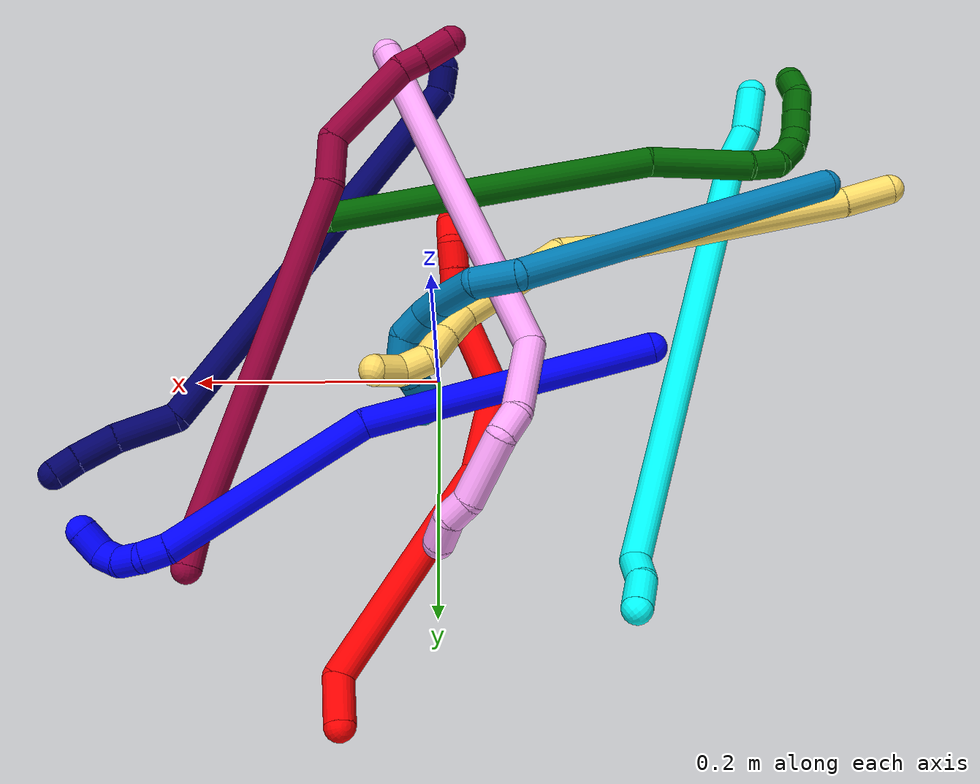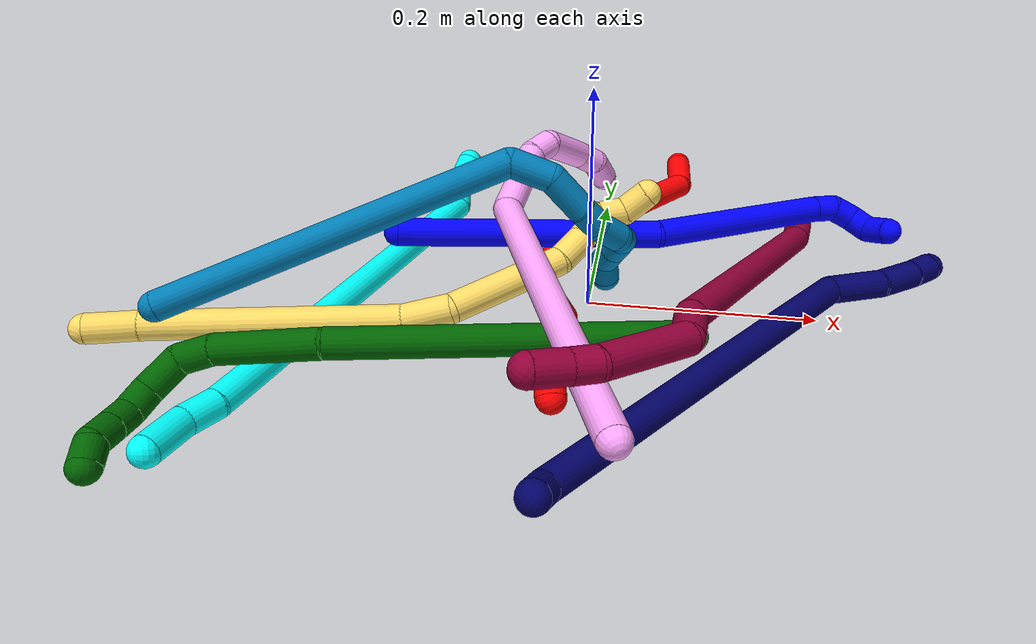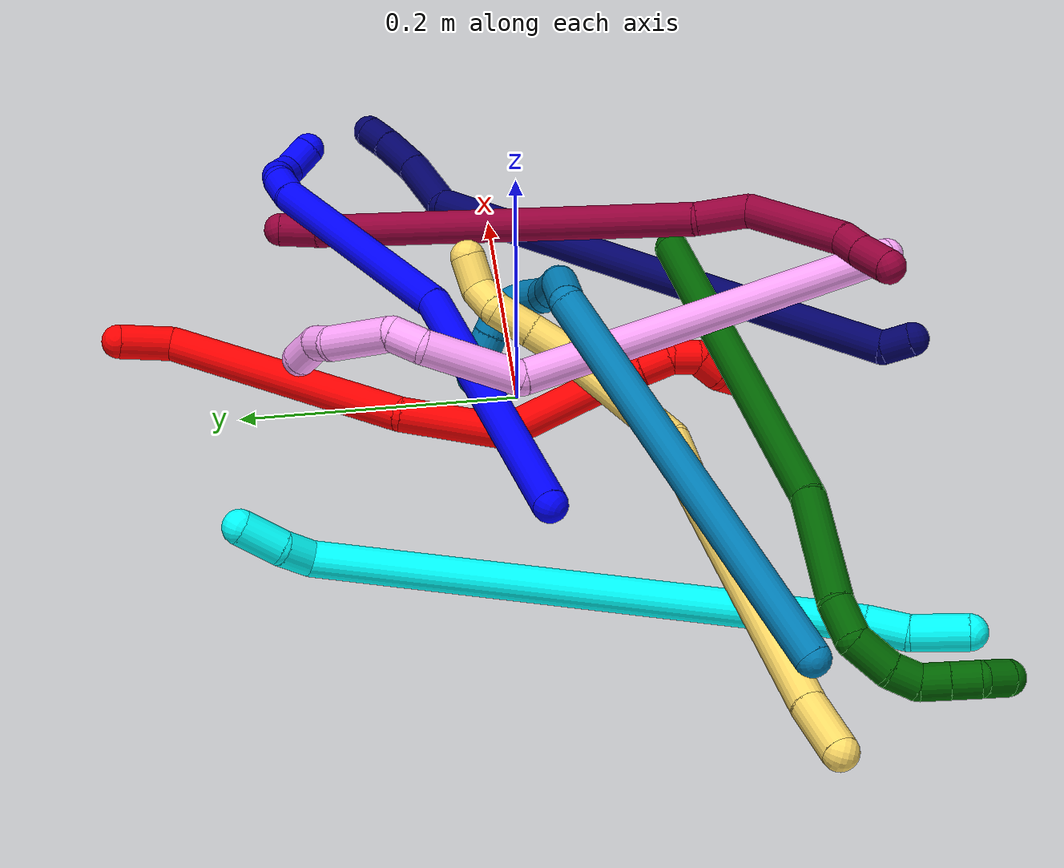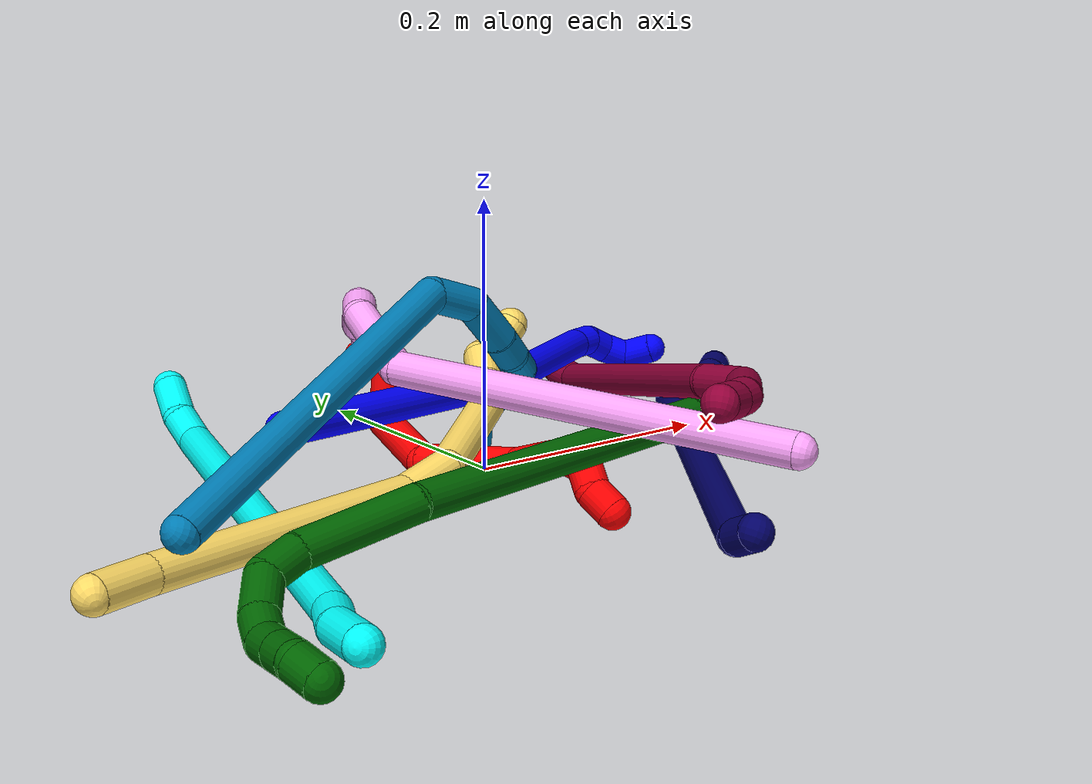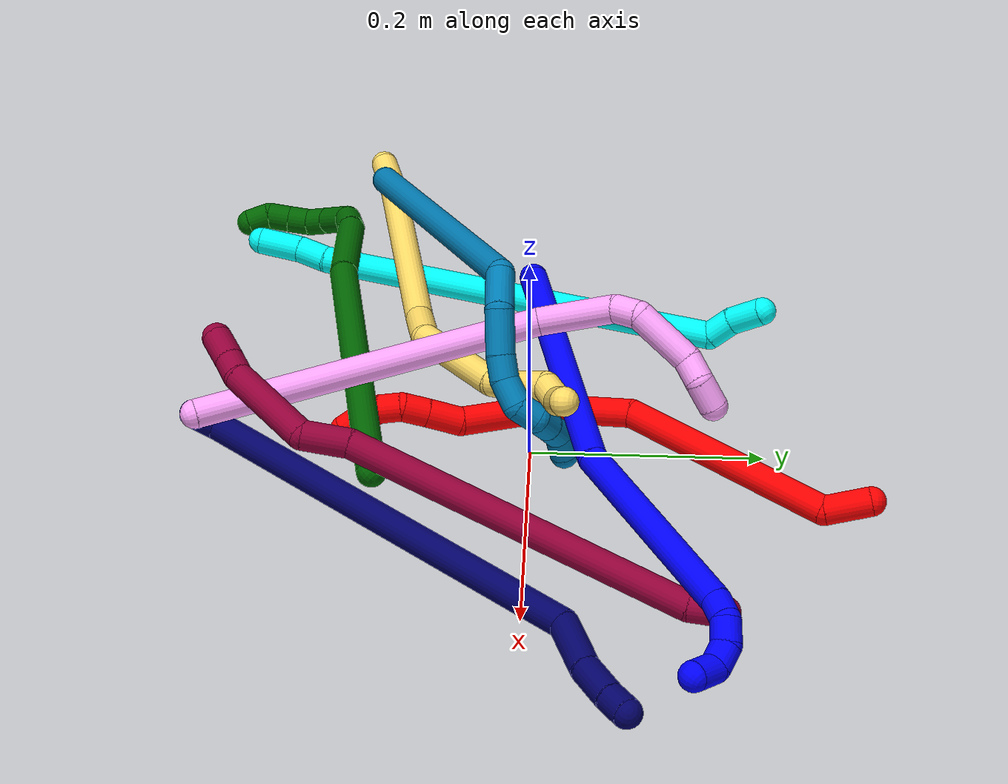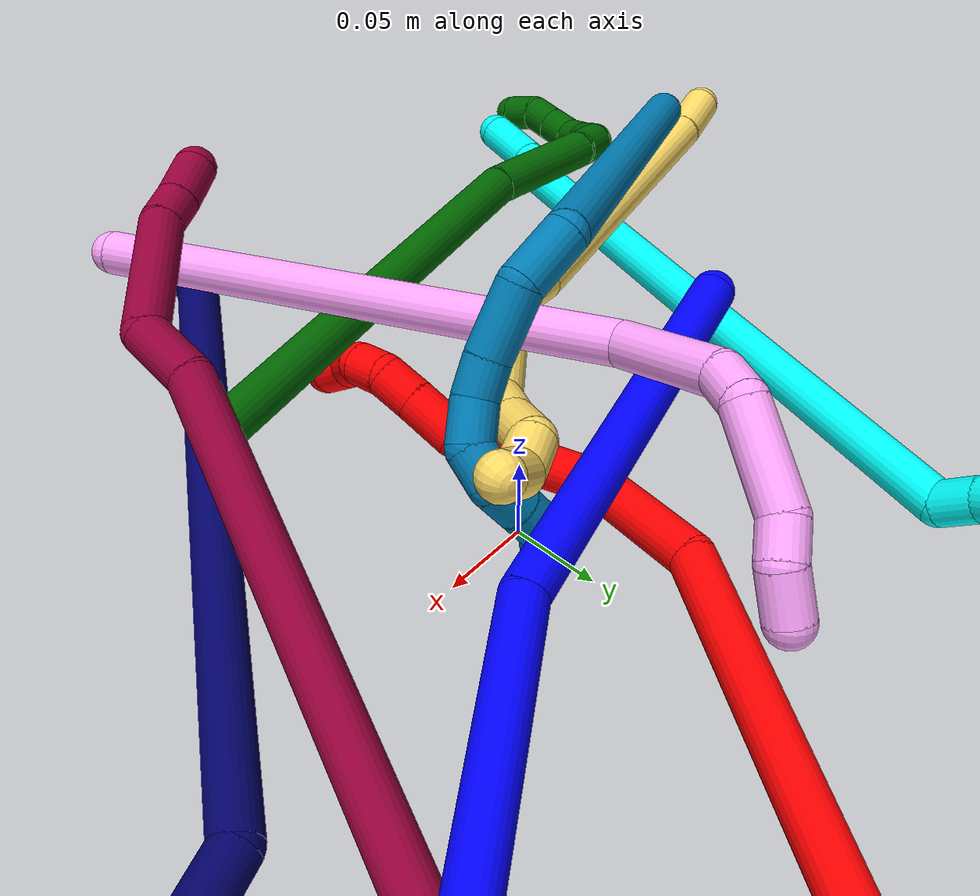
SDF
<sdf version="1.7">
 <world name="default">
  <plugin name="TubeGeneratorPlugin" filename="libtube_generator_plugin.so"/>
  <model name="photoneo_s_sensor">
   <static>1</static>
   <pose>0 0 2 1.57079 1.57079 3.14159</pose>
   <link name="link">
    <inertial><mass>0.1</mass></inertial>
    <sensor name="sensor" type="depth">
     <update_rate>30</update_rate>
     <camera>
      <horizontal_fov>1.22</horizontal_fov>
      <image><width>1920</width><height>1200</height><format>B8G8R8</format></image>
      <clip><near>0.1</near><far>4</far></clip>
      <depth_camera><output>points</output></depth_camera>
     </camera>
     <plugin name="camera_plugin" filename="libgazebo_ros_depth_camera.so">
      <baseline>0.2</baseline>
      <alwaysOn>1</alwaysOn>
      <updateRate>0.0</updateRate>
      <cameraName>camera_ir</cameraName>
      <imageTopicName>/camera/color/image_raw</imageTopicName>
      <cameraInfoTopicName>/camera/color/camera_info</cameraInfoTopicName>
      <depthImageTopicName>/camera/depth/image_raw</depthImageTopicName>
      <depthImageCameraInfoTopicName>/camera/depth/camera_info</depthImageCameraInfoTopicName>
      <pointCloudTopicName>/camera/depth/points</pointCloudTopicName>
      <frameName>fr_optical</frameName>
      <pointCloudCutoff>0.1</pointCloudCutoff>
      <pointCloudCutoffMax>2.0</pointCloudCutoffMax>
      <distortionK1>0</distortionK1>
      <distortionK2>0</distortionK2>
      <distortionK3>0</distortionK3>
      <distortionT1>0</distortionT1>
      <distortionT2>0</distortionT2>
      <CxPrime>0</CxPrime>
      <Cx>0</Cx>
      <Cy>0</Cy>
      <focalLength>0</focalLength>
      <hackBaseline>0</hackBaseline>
     </plugin>
    </sensor>
   </link>
  </model>
  <gravity>0 0 -9.8</gravity>
  <magnetic_field>6e-06 2.3e-05 -4.2e-05</magnetic_field>
  <atmosphere type="adiabatic"/>
  <physics name="default_physics" default="0" type="ode">
   <max_step_size>0.003</max_step_size>
   <real_time_factor>1</real_time_factor>
   <real_time_update_rate>1000</real_time_update_rate>
   <max_contacts>10000</max_contacts>
   <ode>
    <solver>
     <type>quick</type>
     <iters>100</iters>
     <sor>1.3</sor>
     <use_dynamic_moi_rescaling>0</use_dynamic_moi_rescaling>
    </solver>
    <constraints>
     <contact_max_correcting_vel>0</contact_max_correcting_vel>
     <contact_surface_layer>0.001</contact_surface_layer>
     <cfm>0</cfm>
     <erp>0.2</erp>
    </constraints>
   </ode>
  </physics>
  <scene><ambient>0.4 0.4 0.4 1</ambient><background>0.7 0.7 0.7 1</background><shadows>0</shadows></scene>
  <audio><device>default</device></audio>
  <spherical_coordinates>
   <surface_model>EARTH_WGS84</surface_model>
   <latitude_deg>0</latitude_deg>
   <longitude_deg>0</longitude_deg>
   <elevation>0</elevation>
   <heading_deg>0</heading_deg>
  </spherical_coordinates>
  <model name="bin">
   <static>1</static>
   <link name="bottom">
    <collision name="collision-bottom">
     <pose>0 0 -0.01 0 -0 0</pose>
     <geometry><box><size>0.8 0.6 0.02</size></box></geometry>
     <surface>
      <friction><ode><mu>100</mu><mu2>100</mu2></ode></friction>
      <contact><collide_bitmask>65535</collide_bitmask></contact>
     </surface>
    </collision>
   </link>
   <link name="west_wall">
    <collision name="collision-west_wall">
     <pose>-0.41 0 0.1 0 -0 0</pose>
     <geometry><box><size>0.02 0.6 0.2</size></box></geometry>
     <surface>
      <friction><ode><mu>100</mu><mu2>100</mu2></ode></friction>
      <contact><collide_bitmask>65535</collide_bitmask></contact>
     </surface>
    </collision>
   </link>
   <link name="east_wall">
    <collision name="collision-east_wall">
     <pose>0.41 0 0.1 0 -0 0</pose>
     <geometry><box><size>0.02 0.6 0.2</size></box></geometry>
     <surface>
      <friction><ode><mu>100</mu><mu2>100</mu2></ode></friction>
      <contact><collide_bitmask>65535</collide_bitmask></contact>
     </surface>
    </collision>
   </link>
   <link name="south_wall">
    <collision name="collision-south_wall">
     <pose>0 -0.31 0.1 0 -0 0</pose>
     <geometry><box><size>0.8 0.02 0.2</size></box></geometry>
     <surface>
      <friction><ode><mu>100</mu><mu2>100</mu2></ode></friction>
      <contact><collide_bitmask>65535</collide_bitmask></contact>
     </surface>
    </collision>
   </link>
   <link name="north_wall">
    <collision name="collision-north_wall">
     <pose>0 0.31 0.1 0 -0 0</pose>
     <geometry><box><size>0.8 0.02 0.2</size></box></geometry>
     <surface>
      <friction><ode><mu>100</mu><mu2>100</mu2></ode></friction>
      <contact><collide_bitmask>65535</collide_bitmask></contact>
     </surface>
    </collision>
   </link>
  </model>
  <model name="1">
   <static>0</static>
   <link name="1">
    <collision name="collision-cylinder-e_1_1_4">
     <pose>0.026038 0.046804 0.105068 -0.419074 0.222623 -0.04753</pose>
     <geometry><cylinder><radius>0.0125</radius><length>0.235863</length></cylinder></geometry>
     <surface>
      <friction><ode><mu>1.16</mu><mu2>1.16</mu2><slip1>0</slip1><slip2>0</slip2></ode></friction>
      <contact><ode><kp>1e+06</kp><kd>1</kd><max_vel>0</max_vel><min_depth>0.001</min_depth></ode></contact>
     </surface>
    </collision>
    <visual name="visual-cylinder-e_1_1_4">
     <pose>0.026038 0.046804 0.105068 -0.419074 0.222623 -0.04753</pose>
     <geometry><cylinder><radius>0.0125</radius><length>0.235863</length></cylinder></geometry>
     <material><ambient>0 0 1 1</ambient></material>
    </visual>
    <collision name="collision-cylinder-e_2_4_5">
     <pose>0.058382 0.104125 0.298619 -0.118306 0.070656 -0.004186</pose>
     <geometry><cylinder><radius>0.0125</radius><length>0.178659</length></cylinder></geometry>
     <surface>
      <friction><ode><mu>1.16</mu><mu2>1.16</mu2><slip1>0</slip1><slip2>0</slip2></ode></friction>
      <contact><ode><kp>1e+06</kp><kd>1</kd><max_vel>0</max_vel><min_depth>0.001</min_depth></ode></contact>
     </surface>
    </collision>
    <visual name="visual-cylinder-e_2_4_5">
     <pose>0.058382 0.104125 0.298619 -0.118306 0.070656 -0.004186</pose>
     <geometry><cylinder><radius>0.0125</radius><length>0.178659</length></cylinder></geometry>
     <material><ambient>0 0 1 1</ambient></material>
    </visual>
    <collision name="collision-cylinder-e_3_5_6">
     <pose>0.066924 0.117865 0.39684 -0.319651 0.214549 -0.034715</pose>
     <geometry><cylinder><radius>0.0125</radius><length>0.020994</length></cylinder></geometry>
     <surface>
      <friction><ode><mu>1.16</mu><mu2>1.16</mu2><slip1>0</slip1><slip2>0</slip2></ode></friction>
      <contact><ode><kp>1e+06</kp><kd>1</kd><max_vel>0</max_vel><min_depth>0.001</min_depth></ode></contact>
     </surface>
    </collision>
    <visual name="visual-cylinder-e_3_5_6">
     <pose>0.066924 0.117865 0.39684 -0.319651 0.214549 -0.034715</pose>
     <geometry><cylinder><radius>0.0125</radius><length>0.020994</length></cylinder></geometry>
     <material><ambient>0 0 1 1</ambient></material>
    </visual>
    <collision name="collision-cylinder-e_4_6_7">
     <pose>0.068237 0.128144 0.41388 -0.768238 -0.090511 0.036605</pose>
     <geometry><cylinder><radius>0.0125</radius><length>0.020394</length></cylinder></geometry>
     <surface>
      <friction><ode><mu>1.16</mu><mu2>1.16</mu2><slip1>0</slip1><slip2>0</slip2></ode></friction>
      <contact><ode><kp>1e+06</kp><kd>1</kd><max_vel>0</max_vel><min_depth>0.001</min_depth></ode></contact>
     </surface>
    </collision>
    <visual name="visual-cylinder-e_4_6_7">
     <pose>0.068237 0.128144 0.41388 -0.768238 -0.090511 0.036605</pose>
     <geometry><cylinder><radius>0.0125</radius><length>0.020394</length></cylinder></geometry>
     <material><ambient>0 0 1 1</ambient></material>
    </visual>
    <collision name="collision-cylinder-e_5_7_8">
     <pose>0.068521 0.144536 0.424764 -1.20453 0.11999 -0.082541</pose>
     <geometry><cylinder><radius>0.0125</radius><length>0.020141</length></cylinder></geometry>
     <surface>
      <friction><ode><mu>1.16</mu><mu2>1.16</mu2><slip1>0</slip1><slip2>0</slip2></ode></friction>
      <contact><ode><kp>1e+06</kp><kd>1</kd><max_vel>0</max_vel><min_depth>0.001</min_depth></ode></contact>
     </surface>
    </collision>
    <visual name="visual-cylinder-e_5_7_8">
     <pose>0.068521 0.144536 0.424764 -1.20453 0.11999 -0.082541</pose>
     <geometry><cylinder><radius>0.0125</radius><length>0.020141</length></cylinder></geometry>
     <material><ambient>0 0 1 1</ambient></material>
    </visual>
    <collision name="collision-cylinder-e_6_8_2">
     <pose>0.078451 0.162066 0.428667 -1.53145 0.816286 -0.788</pose>
     <geometry><cylinder><radius>0.0125</radius><length>0.023949</length></cylinder></geometry>
     <surface>
      <friction><ode><mu>1.16</mu><mu2>1.16</mu2><slip1>0</slip1><slip2>0</slip2></ode></friction>
      <contact><ode><kp>1e+06</kp><kd>1</kd><max_vel>0</max_vel><min_depth>0.001</min_depth></ode></contact>
     </surface>
    </collision>
    <visual name="visual-cylinder-e_6_8_2">
     <pose>0.078451 0.162066 0.428667 -1.53145 0.816286 -0.788</pose>
     <geometry><cylinder><radius>0.0125</radius><length>0.023949</length></cylinder></geometry>
     <material><ambient>0 0 1 1</ambient></material>
    </visual>
    <collision name="collision-sphere-2">
     <pose>0.087176 0.170262 0.428989 0 -0 0</pose>
     <geometry><sphere><radius>0.0125</radius></sphere></geometry>
     <surface>
      <friction><ode><mu>1.16</mu><mu2>1.16</mu2><slip1>0</slip1><slip2>0</slip2></ode></friction>
      <contact><ode><kp>1e+06</kp><kd>1</kd><max_vel>0</max_vel><min_depth>0.001</min_depth></ode></contact>
     </surface>
    </collision>
    <visual name="visual-sphere-2">
     <pose>0.087176 0.170262 0.428989 0 -0 0</pose>
     <geometry><sphere><radius>0.0125</radius></sphere></geometry>
     <material><ambient>0 0 1 1</ambient></material>
    </visual>
    <collision name="collision-sphere-4">
     <pose>0.052076 0.093607 0.210136 0 -0 0</pose>
     <geometry><sphere><radius>0.0125</radius></sphere></geometry>
     <surface>
      <friction><ode><mu>1.16</mu><mu2>1.16</mu2><slip1>0</slip1><slip2>0</slip2></ode></friction>
      <contact><ode><kp>1e+06</kp><kd>1</kd><max_vel>0</max_vel><min_depth>0.001</min_depth></ode></contact>
     </surface>
    </collision>
    <visual name="visual-sphere-4">
     <pose>0.052076 0.093607 0.210136 0 -0 0</pose>
     <geometry><sphere><radius>0.0125</radius></sphere></geometry>
     <material><ambient>0 0 1 1</ambient></material>
    </visual>
    <collision name="collision-sphere-1">
     <geometry><sphere><radius>0.0125</radius></sphere></geometry>
     <surface>
      <friction><ode><mu>1.16</mu><mu2>1.16</mu2><slip1>0</slip1><slip2>0</slip2></ode></friction>
      <contact><ode><kp>1e+06</kp><kd>1</kd><max_vel>0</max_vel><min_depth>0.001</min_depth></ode></contact>
     </surface>
    </collision>
    <visual name="visual-sphere-1">
     <geometry><sphere><radius>0.0125</radius></sphere></geometry>
     <material><ambient>0 0 1 1</ambient></material>
    </visual>
    <collision name="collision-sphere-8">
     <pose>0.069726 0.153871 0.428344 0 -0 0</pose>
     <geometry><sphere><radius>0.0125</radius></sphere></geometry>
     <surface>
      <friction><ode><mu>1.16</mu><mu2>1.16</mu2><slip1>0</slip1><slip2>0</slip2></ode></friction>
      <contact><ode><kp>1e+06</kp><kd>1</kd><max_vel>0</max_vel><min_depth>0.001</min_depth></ode></contact>
     </surface>
    </collision>
    <visual name="visual-sphere-8">
     <pose>0.069726 0.153871 0.428344 0 -0 0</pose>
     <geometry><sphere><radius>0.0125</radius></sphere></geometry>
     <material><ambient>0 0 1 1</ambient></material>
    </visual>
    <collision name="collision-sphere-5">
     <pose>0.064689 0.114642 0.387103 0 -0 0</pose>
     <geometry><sphere><radius>0.0125</radius></sphere></geometry>
     <surface>
      <friction><ode><mu>1.16</mu><mu2>1.16</mu2><slip1>0</slip1><slip2>0</slip2></ode></friction>
      <contact><ode><kp>1e+06</kp><kd>1</kd><max_vel>0</max_vel><min_depth>0.001</min_depth></ode></contact>
     </surface>
    </collision>
    <visual name="visual-sphere-5">
     <pose>0.064689 0.114642 0.387103 0 -0 0</pose>
     <geometry><sphere><radius>0.0125</radius></sphere></geometry>
     <material><ambient>0 0 1 1</ambient></material>
    </visual>
    <collision name="collision-sphere-6">
     <pose>0.069159 0.121088 0.406577 0 -0 0</pose>
     <geometry><sphere><radius>0.0125</radius></sphere></geometry>
     <surface>
      <friction><ode><mu>1.16</mu><mu2>1.16</mu2><slip1>0</slip1><slip2>0</slip2></ode></friction>
      <contact><ode><kp>1e+06</kp><kd>1</kd><max_vel>0</max_vel><min_depth>0.001</min_depth></ode></contact>
     </surface>
    </collision>
    <visual name="visual-sphere-6">
     <pose>0.069159 0.121088 0.406577 0 -0 0</pose>
     <geometry><sphere><radius>0.0125</radius></sphere></geometry>
     <material><ambient>0 0 1 1</ambient></material>
    </visual>
    <collision name="collision-sphere-7">
     <pose>0.067315 0.135201 0.421183 0 -0 0</pose>
     <geometry><sphere><radius>0.0125</radius></sphere></geometry>
     <surface>
      <friction><ode><mu>1.16</mu><mu2>1.16</mu2><slip1>0</slip1><slip2>0</slip2></ode></friction>
      <contact><ode><kp>1e+06</kp><kd>1</kd><max_vel>0</max_vel><min_depth>0.001</min_depth></ode></contact>
     </surface>
    </collision>
    <visual name="visual-sphere-7">
     <pose>0.067315 0.135201 0.421183 0 -0 0</pose>
     <geometry><sphere><radius>0.0125</radius></sphere></geometry>
     <material><ambient>0 0 1 1</ambient></material>
    </visual>
    <inertial>
     <pose>0.045255 0.083045 0.227452 0 -0 0</pose>
     <mass>0.5</mass>
     <inertia>
      <ixx>0.001513</ixx>
      <ixy>0</ixy>
      <ixz>0</ixz>
      <iyy>0.001453</iyy>
      <iyz>0</iyz>
      <izz>-0.000745</izz>
     </inertia>
    </inertial>
   </link>
   <pose>-0.170767 -0.003198 0.060298 -1.69502 -1.05223 -0.744985</pose>
  </model>
  <model name="2">
   <static>0</static>
   <link name="2">
    <collision name="collision-cylinder-e_1_1_4">
     <pose>-0.001159 -0.018499 -0.007172 1.94064 -0.058373 -0.085209</pose>
     <geometry><cylinder><radius>0.0125</radius><length>0.039749</length></cylinder></geometry>
     <surface>
      <friction><ode><mu>1.16</mu><mu2>1.16</mu2><slip1>0</slip1><slip2>0</slip2></ode></friction>
      <contact><ode><kp>1e+06</kp><kd>1</kd><max_vel>0</max_vel><min_depth>0.001</min_depth></ode></contact>
     </surface>
    </collision>
    <visual name="visual-cylinder-e_1_1_4">
     <pose>-0.001159 -0.018499 -0.007172 1.94064 -0.058373 -0.085209</pose>
     <geometry><cylinder><radius>0.0125</radius><length>0.039749</length></cylinder></geometry>
     <material><ambient>1 0 0 1</ambient></material>
    </visual>
    <collision name="collision-cylinder-e_2_4_5">
     <pose>-0.047528 -0.119012 0.004844 1.34097 -0.492606 -0.393594</pose>
     <geometry><cylinder><radius>0.0125</radius><length>0.191189</length></cylinder></geometry>
     <surface>
      <friction><ode><mu>1.16</mu><mu2>1.16</mu2><slip1>0</slip1><slip2>0</slip2></ode></friction>
      <contact><ode><kp>1e+06</kp><kd>1</kd><max_vel>0</max_vel><min_depth>0.001</min_depth></ode></contact>
     </surface>
    </collision>
    <visual name="visual-cylinder-e_2_4_5">
     <pose>-0.047528 -0.119012 0.004844 1.34097 -0.492606 -0.393594</pose>
     <geometry><cylinder><radius>0.0125</radius><length>0.191189</length></cylinder></geometry>
     <material><ambient>1 0 0 1</ambient></material>
    </visual>
    <collision name="collision-cylinder-e_3_5_6">
     <pose>-0.102846 -0.237162 0.018524 1.72207 -0.269805 -0.31338</pose>
     <geometry><cylinder><radius>0.0125</radius><length>0.075851</length></cylinder></geometry>
     <surface>
      <friction><ode><mu>1.16</mu><mu2>1.16</mu2><slip1>0</slip1><slip2>0</slip2></ode></friction>
      <contact><ode><kp>1e+06</kp><kd>1</kd><max_vel>0</max_vel><min_depth>0.001</min_depth></ode></contact>
     </surface>
    </collision>
    <visual name="visual-cylinder-e_3_5_6">
     <pose>-0.102846 -0.237162 0.018524 1.72207 -0.269805 -0.31338</pose>
     <geometry><cylinder><radius>0.0125</radius><length>0.075851</length></cylinder></geometry>
     <material><ambient>1 0 0 1</ambient></material>
    </visual>
    <collision name="collision-cylinder-e_4_6_7">
     <pose>-0.097903 -0.30947 0.004521 1.80144 0.384882 0.482248</pose>
     <geometry><cylinder><radius>0.0125</radius><length>0.080177</length></cylinder></geometry>
     <surface>
      <friction><ode><mu>1.16</mu><mu2>1.16</mu2><slip1>0</slip1><slip2>0</slip2></ode></friction>
      <contact><ode><kp>1e+06</kp><kd>1</kd><max_vel>0</max_vel><min_depth>0.001</min_depth></ode></contact>
     </surface>
    </collision>
    <visual name="visual-cylinder-e_4_6_7">
     <pose>-0.097903 -0.30947 0.004521 1.80144 0.384882 0.482248</pose>
     <geometry><cylinder><radius>0.0125</radius><length>0.080177</length></cylinder></geometry>
     <material><ambient>1 0 0 1</ambient></material>
    </visual>
    <collision name="collision-cylinder-e_5_7_8">
     <pose>-0.079674 -0.36049 -0.001798 1.4254 0.208718 0.180546</pose>
     <geometry><cylinder><radius>0.0125</radius><length>0.030679</length></cylinder></geometry>
     <surface>
      <friction><ode><mu>1.16</mu><mu2>1.16</mu2><slip1>0</slip1><slip2>0</slip2></ode></friction>
      <contact><ode><kp>1e+06</kp><kd>1</kd><max_vel>0</max_vel><min_depth>0.001</min_depth></ode></contact>
     </surface>
    </collision>
    <visual name="visual-cylinder-e_5_7_8">
     <pose>-0.079674 -0.36049 -0.001798 1.4254 0.208718 0.180546</pose>
     <geometry><cylinder><radius>0.0125</radius><length>0.030679</length></cylinder></geometry>
     <material><ambient>1 0 0 1</ambient></material>
    </visual>
    <collision name="collision-cylinder-e_6_8_9">
     <pose>-0.074063 -0.38608 0.001737 1.44471 0.220962 0.194899</pose>
     <geometry><cylinder><radius>0.0125</radius><length>0.022195</length></cylinder></geometry>
     <surface>
      <friction><ode><mu>1.16</mu><mu2>1.16</mu2><slip1>0</slip1><slip2>0</slip2></ode></friction>
      <contact><ode><kp>1e+06</kp><kd>1</kd><max_vel>0</max_vel><min_depth>0.001</min_depth></ode></contact>
     </surface>
    </collision>
    <visual name="visual-cylinder-e_6_8_9">
     <pose>-0.074063 -0.38608 0.001737 1.44471 0.220962 0.194899</pose>
     <geometry><cylinder><radius>0.0125</radius><length>0.022195</length></cylinder></geometry>
     <material><ambient>1 0 0 1</ambient></material>
    </visual>
    <collision name="collision-cylinder-e_7_9_10">
     <pose>-0.07218 -0.406458 0.000416 1.8424 -0.054888 -0.072248</pose>
     <geometry><cylinder><radius>0.0125</radius><length>0.020035</length></cylinder></geometry>
     <surface>
      <friction><ode><mu>1.16</mu><mu2>1.16</mu2><slip1>0</slip1><slip2>0</slip2></ode></friction>
      <contact><ode><kp>1e+06</kp><kd>1</kd><max_vel>0</max_vel><min_depth>0.001</min_depth></ode></contact>
     </surface>
    </collision>
    <visual name="visual-cylinder-e_7_9_10">
     <pose>-0.07218 -0.406458 0.000416 1.8424 -0.054888 -0.072248</pose>
     <geometry><cylinder><radius>0.0125</radius><length>0.020035</length></cylinder></geometry>
     <material><ambient>1 0 0 1</ambient></material>
    </visual>
    <collision name="collision-cylinder-e_8_10_11">
     <pose>-0.078014 -0.422589 -0.007746 2.27149 -0.556325 -1.10196</pose>
     <geometry><cylinder><radius>0.0125</radius><length>0.020012</length></cylinder></geometry>
     <surface>
      <friction><ode><mu>1.16</mu><mu2>1.16</mu2><slip1>0</slip1><slip2>0</slip2></ode></friction>
      <contact><ode><kp>1e+06</kp><kd>1</kd><max_vel>0</max_vel><min_depth>0.001</min_depth></ode></contact>
     </surface>
    </collision>
    <visual name="visual-cylinder-e_8_10_11">
     <pose>-0.078014 -0.422589 -0.007746 2.27149 -0.556325 -1.10196</pose>
     <geometry><cylinder><radius>0.0125</radius><length>0.020012</length></cylinder></geometry>
     <material><ambient>1 0 0 1</ambient></material>
    </visual>
    <collision name="collision-cylinder-e_9_11_2">
     <pose>-0.084307 -0.436306 -0.02015 2.33523 -0.100563 -0.234873</pose>
     <geometry><cylinder><radius>0.0125</radius><length>0.020112</length></cylinder></geometry>
     <surface>
      <friction><ode><mu>1.16</mu><mu2>1.16</mu2><slip1>0</slip1><slip2>0</slip2></ode></friction>
      <contact><ode><kp>1e+06</kp><kd>1</kd><max_vel>0</max_vel><min_depth>0.001</min_depth></ode></contact>
     </surface>
    </collision>
    <visual name="visual-cylinder-e_9_11_2">
     <pose>-0.084307 -0.436306 -0.02015 2.33523 -0.100563 -0.234873</pose>
     <geometry><cylinder><radius>0.0125</radius><length>0.020112</length></cylinder></geometry>
     <material><ambient>1 0 0 1</ambient></material>
    </visual>
    <collision name="collision-sphere-2">
     <pose>-0.085317 -0.443527 -0.027075 0 -0 0</pose>
     <geometry><sphere><radius>0.0125</radius></sphere></geometry>
     <surface>
      <friction><ode><mu>1.16</mu><mu2>1.16</mu2><slip1>0</slip1><slip2>0</slip2></ode></friction>
      <contact><ode><kp>1e+06</kp><kd>1</kd><max_vel>0</max_vel><min_depth>0.001</min_depth></ode></contact>
     </surface>
    </collision>
    <visual name="visual-sphere-2">
     <pose>-0.085317 -0.443527 -0.027075 0 -0 0</pose>
     <geometry><sphere><radius>0.0125</radius></sphere></geometry>
     <material><ambient>1 0 0 1</ambient></material>
    </visual>
    <collision name="collision-sphere-11">
     <pose>-0.083298 -0.429084 -0.013225 0 -0 0</pose>
     <geometry><sphere><radius>0.0125</radius></sphere></geometry>
     <surface>
      <friction><ode><mu>1.16</mu><mu2>1.16</mu2><slip1>0</slip1><slip2>0</slip2></ode></friction>
      <contact><ode><kp>1e+06</kp><kd>1</kd><max_vel>0</max_vel><min_depth>0.001</min_depth></ode></contact>
     </surface>
    </collision>
    <visual name="visual-sphere-11">
     <pose>-0.083298 -0.429084 -0.013225 0 -0 0</pose>
     <geometry><sphere><radius>0.0125</radius></sphere></geometry>
     <material><ambient>1 0 0 1</ambient></material>
    </visual>
    <collision name="collision-sphere-10">
     <pose>-0.07273 -0.416093 -0.002268 0 -0 0</pose>
     <geometry><sphere><radius>0.0125</radius></sphere></geometry>
     <surface>
      <friction><ode><mu>1.16</mu><mu2>1.16</mu2><slip1>0</slip1><slip2>0</slip2></ode></friction>
      <contact><ode><kp>1e+06</kp><kd>1</kd><max_vel>0</max_vel><min_depth>0.001</min_depth></ode></contact>
     </surface>
    </collision>
    <visual name="visual-sphere-10">
     <pose>-0.07273 -0.416093 -0.002268 0 -0 0</pose>
     <geometry><sphere><radius>0.0125</radius></sphere></geometry>
     <material><ambient>1 0 0 1</ambient></material>
    </visual>
    <collision name="collision-sphere-9">
     <pose>-0.071631 -0.396822 0.003099 0 -0 0</pose>
     <geometry><sphere><radius>0.0125</radius></sphere></geometry>
     <surface>
      <friction><ode><mu>1.16</mu><mu2>1.16</mu2><slip1>0</slip1><slip2>0</slip2></ode></friction>
      <contact><ode><kp>1e+06</kp><kd>1</kd><max_vel>0</max_vel><min_depth>0.001</min_depth></ode></contact>
     </surface>
    </collision>
    <visual name="visual-sphere-9">
     <pose>-0.071631 -0.396822 0.003099 0 -0 0</pose>
     <geometry><sphere><radius>0.0125</radius></sphere></geometry>
     <material><ambient>1 0 0 1</ambient></material>
    </visual>
    <collision name="collision-sphere-4">
     <pose>-0.002319 -0.036998 -0.014344 0 -0 0</pose>
     <geometry><sphere><radius>0.0125</radius></sphere></geometry>
     <surface>
      <friction><ode><mu>1.16</mu><mu2>1.16</mu2><slip1>0</slip1><slip2>0</slip2></ode></friction>
      <contact><ode><kp>1e+06</kp><kd>1</kd><max_vel>0</max_vel><min_depth>0.001</min_depth></ode></contact>
     </surface>
    </collision>
    <visual name="visual-sphere-4">
     <pose>-0.002319 -0.036998 -0.014344 0 -0 0</pose>
     <geometry><sphere><radius>0.0125</radius></sphere></geometry>
     <material><ambient>1 0 0 1</ambient></material>
    </visual>
    <collision name="collision-sphere-1">
     <geometry><sphere><radius>0.0125</radius></sphere></geometry>
     <surface>
      <friction><ode><mu>1.16</mu><mu2>1.16</mu2><slip1>0</slip1><slip2>0</slip2></ode></friction>
      <contact><ode><kp>1e+06</kp><kd>1</kd><max_vel>0</max_vel><min_depth>0.001</min_depth></ode></contact>
     </surface>
    </collision>
    <visual name="visual-sphere-1">
     <geometry><sphere><radius>0.0125</radius></sphere></geometry>
     <material><ambient>1 0 0 1</ambient></material>
    </visual>
    <collision name="collision-sphere-8">
     <pose>-0.076495 -0.375339 0.000376 0 -0 0</pose>
     <geometry><sphere><radius>0.0125</radius></sphere></geometry>
     <surface>
      <friction><ode><mu>1.16</mu><mu2>1.16</mu2><slip1>0</slip1><slip2>0</slip2></ode></friction>
      <contact><ode><kp>1e+06</kp><kd>1</kd><max_vel>0</max_vel><min_depth>0.001</min_depth></ode></contact>
     </surface>
    </collision>
    <visual name="visual-sphere-8">
     <pose>-0.076495 -0.375339 0.000376 0 -0 0</pose>
     <geometry><sphere><radius>0.0125</radius></sphere></geometry>
     <material><ambient>1 0 0 1</ambient></material>
    </visual>
    <collision name="collision-sphere-5">
     <pose>-0.092737 -0.201026 0.024032 0 -0 0</pose>
     <geometry><sphere><radius>0.0125</radius></sphere></geometry>
     <surface>
      <friction><ode><mu>1.16</mu><mu2>1.16</mu2><slip1>0</slip1><slip2>0</slip2></ode></friction>
      <contact><ode><kp>1e+06</kp><kd>1</kd><max_vel>0</max_vel><min_depth>0.001</min_depth></ode></contact>
     </surface>
    </collision>
    <visual name="visual-sphere-5">
     <pose>-0.092737 -0.201026 0.024032 0 -0 0</pose>
     <geometry><sphere><radius>0.0125</radius></sphere></geometry>
     <material><ambient>1 0 0 1</ambient></material>
    </visual>
    <collision name="collision-sphere-6">
     <pose>-0.112955 -0.273298 0.013015 0 -0 0</pose>
     <geometry><sphere><radius>0.0125</radius></sphere></geometry>
     <surface>
      <friction><ode><mu>1.16</mu><mu2>1.16</mu2><slip1>0</slip1><slip2>0</slip2></ode></friction>
      <contact><ode><kp>1e+06</kp><kd>1</kd><max_vel>0</max_vel><min_depth>0.001</min_depth></ode></contact>
     </surface>
    </collision>
    <visual name="visual-sphere-6">
     <pose>-0.112955 -0.273298 0.013015 0 -0 0</pose>
     <geometry><sphere><radius>0.0125</radius></sphere></geometry>
     <material><ambient>1 0 0 1</ambient></material>
    </visual>
    <collision name="collision-sphere-7">
     <pose>-0.082852 -0.345642 -0.003973 0 -0 0</pose>
     <geometry><sphere><radius>0.0125</radius></sphere></geometry>
     <surface>
      <friction><ode><mu>1.16</mu><mu2>1.16</mu2><slip1>0</slip1><slip2>0</slip2></ode></friction>
      <contact><ode><kp>1e+06</kp><kd>1</kd><max_vel>0</max_vel><min_depth>0.001</min_depth></ode></contact>
     </surface>
    </collision>
    <visual name="visual-sphere-7">
     <pose>-0.082852 -0.345642 -0.003973 0 -0 0</pose>
     <geometry><sphere><radius>0.0125</radius></sphere></geometry>
     <material><ambient>1 0 0 1</ambient></material>
    </visual>
    <inertial>
     <pose>-0.067149 -0.222589 0.00368 0 -0 0</pose>
     <mass>0.5</mass>
     <inertia><ixx>0.00037</ixx><ixy>0</ixy><ixz>0</ixz><iyy>-5e-06</iyy><iyz>0</iyz><izz>0.00087</izz></inertia>
    </inertial>
   </link>
   <pose>0.072074 0.284466 0.020399 -0.143994 -0.503778 0.020752</pose>
  </model>
  <model name="3">
   <static>0</static>
   <link name="3">
    <collision name="collision-cylinder-e_1_1_4">
     <pose>0.001637 0.012951 -0.014633 -2.4171 0.083598 -0.21983</pose>
     <geometry><cylinder><radius>0.0125</radius><length>0.03922</length></cylinder></geometry>
     <surface>
      <friction><ode><mu>1.16</mu><mu2>1.16</mu2><slip1>0</slip1><slip2>0</slip2></ode></friction>
      <contact><ode><kp>1e+06</kp><kd>1</kd><max_vel>0</max_vel><min_depth>0.001</min_depth></ode></contact>
     </surface>
    </collision>
    <visual name="visual-cylinder-e_1_1_4">
     <pose>0.001637 0.012951 -0.014633 -2.4171 0.083598 -0.21983</pose>
     <geometry><cylinder><radius>0.0125</radius><length>0.03922</length></cylinder></geometry>
     <material><ambient>0.003922 1 0.996078 1</ambient></material>
    </visual>
    <collision name="collision-cylinder-e_2_4_5">
     <pose>0.005544 0.032281 -0.042396 -2.68933 0.154228 -0.648019</pose>
     <geometry><cylinder><radius>0.0125</radius><length>0.029544</length></cylinder></geometry>
     <surface>
      <friction><ode><mu>1.16</mu><mu2>1.16</mu2><slip1>0</slip1><slip2>0</slip2></ode></friction>
      <contact><ode><kp>1e+06</kp><kd>1</kd><max_vel>0</max_vel><min_depth>0.001</min_depth></ode></contact>
     </surface>
    </collision>
    <visual name="visual-cylinder-e_2_4_5">
     <pose>0.005544 0.032281 -0.042396 -2.68933 0.154228 -0.648019</pose>
     <geometry><cylinder><radius>0.0125</radius><length>0.029544</length></cylinder></geometry>
     <material><ambient>0.003922 1 0.996078 1</ambient></material>
    </visual>
    <collision name="collision-cylinder-e_3_5_6">
     <pose>0.043746 0.150104 -0.201927 -2.49095 0.192865 -0.558571</pose>
     <geometry><cylinder><radius>0.0125</radius><length>0.374938</length></cylinder></geometry>
     <surface>
      <friction><ode><mu>1.16</mu><mu2>1.16</mu2><slip1>0</slip1><slip2>0</slip2></ode></friction>
      <contact><ode><kp>1e+06</kp><kd>1</kd><max_vel>0</max_vel><min_depth>0.001</min_depth></ode></contact>
     </surface>
    </collision>
    <visual name="visual-cylinder-e_3_5_6">
     <pose>0.043746 0.150104 -0.201927 -2.49095 0.192865 -0.558571</pose>
     <geometry><cylinder><radius>0.0125</radius><length>0.374938</length></cylinder></geometry>
     <material><ambient>0.003922 1 0.996078 1</ambient></material>
    </visual>
    <collision name="collision-cylinder-e_4_6_7">
     <pose>0.088566 0.269827 -0.351369 -1.92255 0.789247 -1.07566</pose>
     <geometry><cylinder><radius>0.0125</radius><length>0.025042</length></cylinder></geometry>
     <surface>
      <friction><ode><mu>1.16</mu><mu2>1.16</mu2><slip1>0</slip1><slip2>0</slip2></ode></friction>
      <contact><ode><kp>1e+06</kp><kd>1</kd><max_vel>0</max_vel><min_depth>0.001</min_depth></ode></contact>
     </surface>
    </collision>
    <visual name="visual-cylinder-e_4_6_7">
     <pose>0.088566 0.269827 -0.351369 -1.92255 0.789247 -1.07566</pose>
     <geometry><cylinder><radius>0.0125</radius><length>0.025042</length></cylinder></geometry>
     <material><ambient>0.003922 1 0.996078 1</ambient></material>
    </visual>
    <collision name="collision-cylinder-e_5_7_2">
     <pose>0.107974 0.286167 -0.362689 -2.36978 0.738503 -1.52221</pose>
     <geometry><cylinder><radius>0.0125</radius><length>0.031256</length></cylinder></geometry>
     <surface>
      <friction><ode><mu>1.16</mu><mu2>1.16</mu2><slip1>0</slip1><slip2>0</slip2></ode></friction>
      <contact><ode><kp>1e+06</kp><kd>1</kd><max_vel>0</max_vel><min_depth>0.001</min_depth></ode></contact>
     </surface>
    </collision>
    <visual name="visual-cylinder-e_5_7_2">
     <pose>0.107974 0.286167 -0.362689 -2.36978 0.738503 -1.52221</pose>
     <geometry><cylinder><radius>0.0125</radius><length>0.031256</length></cylinder></geometry>
     <material><ambient>0.003922 1 0.996078 1</ambient></material>
    </visual>
    <collision name="collision-sphere-2">
     <pose>0.118495 0.294227 -0.370971 0 -0 0</pose>
     <geometry><sphere><radius>0.0125</radius></sphere></geometry>
     <surface>
      <friction><ode><mu>1.16</mu><mu2>1.16</mu2><slip1>0</slip1><slip2>0</slip2></ode></friction>
      <contact><ode><kp>1e+06</kp><kd>1</kd><max_vel>0</max_vel><min_depth>0.001</min_depth></ode></contact>
     </surface>
    </collision>
    <visual name="visual-sphere-2">
     <pose>0.118495 0.294227 -0.370971 0 -0 0</pose>
     <geometry><sphere><radius>0.0125</radius></sphere></geometry>
     <material><ambient>0.003922 1 0.996078 1</ambient></material>
    </visual>
    <collision name="collision-sphere-7">
     <pose>0.097454 0.278107 -0.354407 0 -0 0</pose>
     <geometry><sphere><radius>0.0125</radius></sphere></geometry>
     <surface>
      <friction><ode><mu>1.16</mu><mu2>1.16</mu2><slip1>0</slip1><slip2>0</slip2></ode></friction>
      <contact><ode><kp>1e+06</kp><kd>1</kd><max_vel>0</max_vel><min_depth>0.001</min_depth></ode></contact>
     </surface>
    </collision>
    <visual name="visual-sphere-7">
     <pose>0.097454 0.278107 -0.354407 0 -0 0</pose>
     <geometry><sphere><radius>0.0125</radius></sphere></geometry>
     <material><ambient>0.003922 1 0.996078 1</ambient></material>
    </visual>
    <collision name="collision-sphere-6">
     <pose>0.079678 0.261548 -0.34833 0 -0 0</pose>
     <geometry><sphere><radius>0.0125</radius></sphere></geometry>
     <surface>
      <friction><ode><mu>1.16</mu><mu2>1.16</mu2><slip1>0</slip1><slip2>0</slip2></ode></friction>
      <contact><ode><kp>1e+06</kp><kd>1</kd><max_vel>0</max_vel><min_depth>0.001</min_depth></ode></contact>
     </surface>
    </collision>
    <visual name="visual-sphere-6">
     <pose>0.079678 0.261548 -0.34833 0 -0 0</pose>
     <geometry><sphere><radius>0.0125</radius></sphere></geometry>
     <material><ambient>0.003922 1 0.996078 1</ambient></material>
    </visual>
    <collision name="collision-sphere-5">
     <pose>0.007813 0.03866 -0.055525 0 -0 0</pose>
     <geometry><sphere><radius>0.0125</radius></sphere></geometry>
     <surface>
      <friction><ode><mu>1.16</mu><mu2>1.16</mu2><slip1>0</slip1><slip2>0</slip2></ode></friction>
      <contact><ode><kp>1e+06</kp><kd>1</kd><max_vel>0</max_vel><min_depth>0.001</min_depth></ode></contact>
     </surface>
    </collision>
    <visual name="visual-sphere-5">
     <pose>0.007813 0.03866 -0.055525 0 -0 0</pose>
     <geometry><sphere><radius>0.0125</radius></sphere></geometry>
     <material><ambient>0.003922 1 0.996078 1</ambient></material>
    </visual>
    <collision name="collision-sphere-1">
     <geometry><sphere><radius>0.0125</radius></sphere></geometry>
     <surface>
      <friction><ode><mu>1.16</mu><mu2>1.16</mu2><slip1>0</slip1><slip2>0</slip2></ode></friction>
      <contact><ode><kp>1e+06</kp><kd>1</kd><max_vel>0</max_vel><min_depth>0.001</min_depth></ode></contact>
     </surface>
    </collision>
    <visual name="visual-sphere-1">
     <geometry><sphere><radius>0.0125</radius></sphere></geometry>
     <material><ambient>0.003922 1 0.996078 1</ambient></material>
    </visual>
    <collision name="collision-sphere-4">
     <pose>0.003275 0.025903 -0.029267 0 -0 0</pose>
     <geometry><sphere><radius>0.0125</radius></sphere></geometry>
     <surface>
      <friction><ode><mu>1.16</mu><mu2>1.16</mu2><slip1>0</slip1><slip2>0</slip2></ode></friction>
      <contact><ode><kp>1e+06</kp><kd>1</kd><max_vel>0</max_vel><min_depth>0.001</min_depth></ode></contact>
     </surface>
    </collision>
    <visual name="visual-sphere-4">
     <pose>0.003275 0.025903 -0.029267 0 -0 0</pose>
     <geometry><sphere><radius>0.0125</radius></sphere></geometry>
     <material><ambient>0.003922 1 0.996078 1</ambient></material>
    </visual>
    <inertial>
     <pose>0.044445 0.146886 -0.195344 0 -0 0</pose>
     <mass>0.5</mass>
     <inertia>
      <ixx>0.001387</ixx>
      <ixy>0</ixy>
      <ixz>0</ixz>
      <iyy>-0.004984</iyy>
      <iyz>0</iyz>
      <izz>-0.003508</izz>
     </inertia>
    </inertial>
   </link>
   <pose>-0.277291 -0.267767 0.017058 -0.143277 -1.35097 0.797984</pose>
  </model>
  <model name="4">
   <static>0</static>
   <link name="4">
    <collision name="collision-cylinder-e_1_1_4">
     <pose>-0.008053 0.013584 0.151103 -0.089661 -0.053033 0.00238</pose>
     <geometry><cylinder><radius>0.0125</radius><length>0.303851</length></cylinder></geometry>
     <surface>
      <friction><ode><mu>1.16</mu><mu2>1.16</mu2><slip1>0</slip1><slip2>0</slip2></ode></friction>
      <contact><ode><kp>1e+06</kp><kd>1</kd><max_vel>0</max_vel><min_depth>0.001</min_depth></ode></contact>
     </surface>
    </collision>
    <visual name="visual-cylinder-e_1_1_4">
     <pose>-0.008053 0.013584 0.151103 -0.089661 -0.053033 0.00238</pose>
     <geometry><cylinder><radius>0.0125</radius><length>0.303851</length></cylinder></geometry>
     <material><ambient>1 0.65098 0.996078 1</ambient></material>
    </visual>
    <collision name="collision-cylinder-e_2_4_5">
     <pose>-0.00258 0.044665 0.330073 -0.560609 0.39003 -0.113607</pose>
     <geometry><cylinder><radius>0.0125</radius><length>0.071154</length></cylinder></geometry>
     <surface>
      <friction><ode><mu>1.16</mu><mu2>1.16</mu2><slip1>0</slip1><slip2>0</slip2></ode></friction>
      <contact><ode><kp>1e+06</kp><kd>1</kd><max_vel>0</max_vel><min_depth>0.001</min_depth></ode></contact>
     </surface>
    </collision>
    <visual name="visual-cylinder-e_2_4_5">
     <pose>-0.00258 0.044665 0.330073 -0.560609 0.39003 -0.113607</pose>
     <geometry><cylinder><radius>0.0125</radius><length>0.071154</length></cylinder></geometry>
     <material><ambient>1 0.65098 0.996078 1</ambient></material>
    </visual>
    <collision name="collision-cylinder-e_3_5_6">
     <pose>0.014028 0.071757 0.36429 -0.986395 0.261564 -0.141163</pose>
     <geometry><cylinder><radius>0.0125</radius><length>0.023823</length></cylinder></geometry>
     <surface>
      <friction><ode><mu>1.16</mu><mu2>1.16</mu2><slip1>0</slip1><slip2>0</slip2></ode></friction>
      <contact><ode><kp>1e+06</kp><kd>1</kd><max_vel>0</max_vel><min_depth>0.001</min_depth></ode></contact>
     </surface>
    </collision>
    <visual name="visual-cylinder-e_3_5_6">
     <pose>0.014028 0.071757 0.36429 -0.986395 0.261564 -0.141163</pose>
     <geometry><cylinder><radius>0.0125</radius><length>0.023823</length></cylinder></geometry>
     <material><ambient>1 0.65098 0.996078 1</ambient></material>
    </visual>
    <collision name="collision-cylinder-e_4_6_7">
     <pose>0.007348 0.104304 0.381659 -1.12312 -0.366054 0.231856</pose>
     <geometry><cylinder><radius>0.0125</radius><length>0.054532</length></cylinder></geometry>
     <surface>
      <friction><ode><mu>1.16</mu><mu2>1.16</mu2><slip1>0</slip1><slip2>0</slip2></ode></friction>
      <contact><ode><kp>1e+06</kp><kd>1</kd><max_vel>0</max_vel><min_depth>0.001</min_depth></ode></contact>
     </surface>
    </collision>
    <visual name="visual-cylinder-e_4_6_7">
     <pose>0.007348 0.104304 0.381659 -1.12312 -0.366054 0.231856</pose>
     <geometry><cylinder><radius>0.0125</radius><length>0.054532</length></cylinder></geometry>
     <material><ambient>1 0.65098 0.996078 1</ambient></material>
    </visual>
    <collision name="collision-cylinder-e_5_7_8">
     <pose>-0.00609 0.13707 0.393221 -1.51566 -0.358134 0.339288</pose>
     <geometry><cylinder><radius>0.0125</radius><length>0.020992</length></cylinder></geometry>
     <surface>
      <friction><ode><mu>1.16</mu><mu2>1.16</mu2><slip1>0</slip1><slip2>0</slip2></ode></friction>
      <contact><ode><kp>1e+06</kp><kd>1</kd><max_vel>0</max_vel><min_depth>0.001</min_depth></ode></contact>
     </surface>
    </collision>
    <visual name="visual-cylinder-e_5_7_8">
     <pose>-0.00609 0.13707 0.393221 -1.51566 -0.358134 0.339288</pose>
     <geometry><cylinder><radius>0.0125</radius><length>0.020992</length></cylinder></geometry>
     <material><ambient>1 0.65098 0.996078 1</ambient></material>
    </visual>
    <collision name="collision-cylinder-e_6_8_2">
     <pose>-0.018841 0.155567 0.396367 -1.2794 -0.785818 0.598274</pose>
     <geometry><cylinder><radius>0.0125</radius><length>0.025648</length></cylinder></geometry>
     <surface>
      <friction><ode><mu>1.16</mu><mu2>1.16</mu2><slip1>0</slip1><slip2>0</slip2></ode></friction>
      <contact><ode><kp>1e+06</kp><kd>1</kd><max_vel>0</max_vel><min_depth>0.001</min_depth></ode></contact>
     </surface>
    </collision>
    <visual name="visual-cylinder-e_6_8_2">
     <pose>-0.018841 0.155567 0.396367 -1.2794 -0.785818 0.598274</pose>
     <geometry><cylinder><radius>0.0125</radius><length>0.025648</length></cylinder></geometry>
     <material><ambient>1 0.65098 0.996078 1</ambient></material>
    </visual>
    <collision name="collision-sphere-2">
     <pose>-0.027913 0.164249 0.398971 0 -0 0</pose>
     <geometry><sphere><radius>0.0125</radius></sphere></geometry>
     <surface>
      <friction><ode><mu>1.16</mu><mu2>1.16</mu2><slip1>0</slip1><slip2>0</slip2></ode></friction>
      <contact><ode><kp>1e+06</kp><kd>1</kd><max_vel>0</max_vel><min_depth>0.001</min_depth></ode></contact>
     </surface>
    </collision>
    <visual name="visual-sphere-2">
     <pose>-0.027913 0.164249 0.398971 0 -0 0</pose>
     <geometry><sphere><radius>0.0125</radius></sphere></geometry>
     <material><ambient>1 0.65098 0.996078 1</ambient></material>
    </visual>
    <collision name="collision-sphere-4">
     <pose>-0.016107 0.027169 0.302205 0 -0 0</pose>
     <geometry><sphere><radius>0.0125</radius></sphere></geometry>
     <surface>
      <friction><ode><mu>1.16</mu><mu2>1.16</mu2><slip1>0</slip1><slip2>0</slip2></ode></friction>
      <contact><ode><kp>1e+06</kp><kd>1</kd><max_vel>0</max_vel><min_depth>0.001</min_depth></ode></contact>
     </surface>
    </collision>
    <visual name="visual-sphere-4">
     <pose>-0.016107 0.027169 0.302205 0 -0 0</pose>
     <geometry><sphere><radius>0.0125</radius></sphere></geometry>
     <material><ambient>1 0.65098 0.996078 1</ambient></material>
    </visual>
    <collision name="collision-sphere-1">
     <geometry><sphere><radius>0.0125</radius></sphere></geometry>
     <surface>
      <friction><ode><mu>1.16</mu><mu2>1.16</mu2><slip1>0</slip1><slip2>0</slip2></ode></friction>
      <contact><ode><kp>1e+06</kp><kd>1</kd><max_vel>0</max_vel><min_depth>0.001</min_depth></ode></contact>
     </surface>
    </collision>
    <visual name="visual-sphere-1">
     <geometry><sphere><radius>0.0125</radius></sphere></geometry>
     <material><ambient>1 0.65098 0.996078 1</ambient></material>
    </visual>
    <collision name="collision-sphere-8">
     <pose>-0.009769 0.146885 0.393763 0 -0 0</pose>
     <geometry><sphere><radius>0.0125</radius></sphere></geometry>
     <surface>
      <friction><ode><mu>1.16</mu><mu2>1.16</mu2><slip1>0</slip1><slip2>0</slip2></ode></friction>
      <contact><ode><kp>1e+06</kp><kd>1</kd><max_vel>0</max_vel><min_depth>0.001</min_depth></ode></contact>
     </surface>
    </collision>
    <visual name="visual-sphere-8">
     <pose>-0.009769 0.146885 0.393763 0 -0 0</pose>
     <geometry><sphere><radius>0.0125</radius></sphere></geometry>
     <material><ambient>1 0.65098 0.996078 1</ambient></material>
    </visual>
    <collision name="collision-sphere-5">
     <pose>0.010947 0.06216 0.357942 0 -0 0</pose>
     <geometry><sphere><radius>0.0125</radius></sphere></geometry>
     <surface>
      <friction><ode><mu>1.16</mu><mu2>1.16</mu2><slip1>0</slip1><slip2>0</slip2></ode></friction>
      <contact><ode><kp>1e+06</kp><kd>1</kd><max_vel>0</max_vel><min_depth>0.001</min_depth></ode></contact>
     </surface>
    </collision>
    <visual name="visual-sphere-5">
     <pose>0.010947 0.06216 0.357942 0 -0 0</pose>
     <geometry><sphere><radius>0.0125</radius></sphere></geometry>
     <material><ambient>1 0.65098 0.996078 1</ambient></material>
    </visual>
    <collision name="collision-sphere-6">
     <pose>0.017108 0.081354 0.370638 0 -0 0</pose>
     <geometry><sphere><radius>0.0125</radius></sphere></geometry>
     <surface>
      <friction><ode><mu>1.16</mu><mu2>1.16</mu2><slip1>0</slip1><slip2>0</slip2></ode></friction>
      <contact><ode><kp>1e+06</kp><kd>1</kd><max_vel>0</max_vel><min_depth>0.001</min_depth></ode></contact>
     </surface>
    </collision>
    <visual name="visual-sphere-6">
     <pose>0.017108 0.081354 0.370638 0 -0 0</pose>
     <geometry><sphere><radius>0.0125</radius></sphere></geometry>
     <material><ambient>1 0.65098 0.996078 1</ambient></material>
    </visual>
    <collision name="collision-sphere-7">
     <pose>-0.002411 0.127255 0.39268 0 -0 0</pose>
     <geometry><sphere><radius>0.0125</radius></sphere></geometry>
     <surface>
      <friction><ode><mu>1.16</mu><mu2>1.16</mu2><slip1>0</slip1><slip2>0</slip2></ode></friction>
      <contact><ode><kp>1e+06</kp><kd>1</kd><max_vel>0</max_vel><min_depth>0.001</min_depth></ode></contact>
     </surface>
    </collision>
    <visual name="visual-sphere-7">
     <pose>-0.002411 0.127255 0.39268 0 -0 0</pose>
     <geometry><sphere><radius>0.0125</radius></sphere></geometry>
     <material><ambient>1 0.65098 0.996078 1</ambient></material>
    </visual>
    <inertial>
     <pose>-0.005013 0.043141 0.234621 0 -0 0</pose>
     <mass>0.5</mass>
     <inertia><ixx>0.0024</ixx><ixy>0</ixy><ixz>0</ixz><iyy>0.002399</iyy><iyz>0</iyz><izz>-9.4e-05</izz></inertia>
    </inertial>
   </link>
   <pose>0.04348 -0.275387 0.071562 -1.0725 -1.3168 -0.015001</pose>
  </model>
  <model name="5">
   <static>0</static>
   <link name="5">
    <collision name="collision-cylinder-e_1_1_4">
     <pose>0.016328 0.007244 -0.01096 -2.5576 0.893257 -2.02057</pose>
     <geometry><cylinder><radius>0.0125</radius><length>0.041915</length></cylinder></geometry>
     <surface>
      <friction><ode><mu>1.16</mu><mu2>1.16</mu2><slip1>0</slip1><slip2>0</slip2></ode></friction>
      <contact><ode><kp>1e+06</kp><kd>1</kd><max_vel>0</max_vel><min_depth>0.001</min_depth></ode></contact>
     </surface>
    </collision>
    <visual name="visual-cylinder-e_1_1_4">
     <pose>0.016328 0.007244 -0.01096 -2.5576 0.893257 -2.02057</pose>
     <geometry><cylinder><radius>0.0125</radius><length>0.041915</length></cylinder></geometry>
     <material><ambient>1 0.858824 0.4 1</ambient></material>
    </visual>
    <collision name="collision-cylinder-e_2_4_5">
     <pose>0.115733 0.055495 -0.068613 -2.42092 0.928559 -1.85154</pose>
     <geometry><cylinder><radius>0.0125</radius><length>0.207495</length></cylinder></geometry>
     <surface>
      <friction><ode><mu>1.16</mu><mu2>1.16</mu2><slip1>0</slip1><slip2>0</slip2></ode></friction>
      <contact><ode><kp>1e+06</kp><kd>1</kd><max_vel>0</max_vel><min_depth>0.001</min_depth></ode></contact>
     </surface>
    </collision>
    <visual name="visual-cylinder-e_2_4_5">
     <pose>0.115733 0.055495 -0.068613 -2.42092 0.928559 -1.85154</pose>
     <geometry><cylinder><radius>0.0125</radius><length>0.207495</length></cylinder></geometry>
     <material><ambient>1 0.858824 0.4 1</ambient></material>
    </visual>
    <collision name="collision-cylinder-e_3_5_6">
     <pose>0.212347 0.108195 -0.12545 -2.28549 0.718571 -1.37743</pose>
     <geometry><cylinder><radius>0.0125</radius><length>0.041127</length></cylinder></geometry>
     <surface>
      <friction><ode><mu>1.16</mu><mu2>1.16</mu2><slip1>0</slip1><slip2>0</slip2></ode></friction>
      <contact><ode><kp>1e+06</kp><kd>1</kd><max_vel>0</max_vel><min_depth>0.001</min_depth></ode></contact>
     </surface>
    </collision>
    <visual name="visual-cylinder-e_3_5_6">
     <pose>0.212347 0.108195 -0.12545 -2.28549 0.718571 -1.37743</pose>
     <geometry><cylinder><radius>0.0125</radius><length>0.041127</length></cylinder></geometry>
     <material><ambient>1 0.858824 0.4 1</ambient></material>
    </visual>
    <collision name="collision-cylinder-e_4_6_7">
     <pose>0.251125 0.134683 -0.177723 -2.80382 0.51452 -1.99151</pose>
     <geometry><cylinder><radius>0.0125</radius><length>0.102584</length></cylinder></geometry>
     <surface>
      <friction><ode><mu>1.16</mu><mu2>1.16</mu2><slip1>0</slip1><slip2>0</slip2></ode></friction>
      <contact><ode><kp>1e+06</kp><kd>1</kd><max_vel>0</max_vel><min_depth>0.001</min_depth></ode></contact>
     </surface>
    </collision>
    <visual name="visual-cylinder-e_4_6_7">
     <pose>0.251125 0.134683 -0.177723 -2.80382 0.51452 -1.99151</pose>
     <geometry><cylinder><radius>0.0125</radius><length>0.102584</length></cylinder></geometry>
     <material><ambient>1 0.858824 0.4 1</ambient></material>
    </visual>
    <collision name="collision-cylinder-e_5_7_8">
     <pose>0.278925 0.153169 -0.233872 -2.88425 0.174661 -1.18981</pose>
     <geometry><cylinder><radius>0.0125</radius><length>0.029445</length></cylinder></geometry>
     <surface>
      <friction><ode><mu>1.16</mu><mu2>1.16</mu2><slip1>0</slip1><slip2>0</slip2></ode></friction>
      <contact><ode><kp>1e+06</kp><kd>1</kd><max_vel>0</max_vel><min_depth>0.001</min_depth></ode></contact>
     </surface>
    </collision>
    <visual name="visual-cylinder-e_5_7_8">
     <pose>0.278925 0.153169 -0.233872 -2.88425 0.174661 -1.18981</pose>
     <geometry><cylinder><radius>0.0125</radius><length>0.029445</length></cylinder></geometry>
     <material><ambient>1 0.858824 0.4 1</ambient></material>
    </visual>
    <collision name="collision-cylinder-e_6_8_9">
     <pose>0.282487 0.160538 -0.262008 -2.88663 0.068634 -0.523386</pose>
     <geometry><cylinder><radius>0.0125</radius><length>0.029242</length></cylinder></geometry>
     <surface>
      <friction><ode><mu>1.16</mu><mu2>1.16</mu2><slip1>0</slip1><slip2>0</slip2></ode></friction>
      <contact><ode><kp>1e+06</kp><kd>1</kd><max_vel>0</max_vel><min_depth>0.001</min_depth></ode></contact>
     </surface>
    </collision>
    <visual name="visual-cylinder-e_6_8_9">
     <pose>0.282487 0.160538 -0.262008 -2.88663 0.068634 -0.523386</pose>
     <geometry><cylinder><radius>0.0125</radius><length>0.029242</length></cylinder></geometry>
     <material><ambient>1 0.858824 0.4 1</ambient></material>
    </visual>
    <collision name="collision-cylinder-e_7_9_10">
     <pose>0.291305 0.167914 -0.283774 -2.69144 0.743586 -2.07973</pose>
     <geometry><cylinder><radius>0.0125</radius><length>0.023091</length></cylinder></geometry>
     <surface>
      <friction><ode><mu>1.16</mu><mu2>1.16</mu2><slip1>0</slip1><slip2>0</slip2></ode></friction>
      <contact><ode><kp>1e+06</kp><kd>1</kd><max_vel>0</max_vel><min_depth>0.001</min_depth></ode></contact>
     </surface>
    </collision>
    <visual name="visual-cylinder-e_7_9_10">
     <pose>0.291305 0.167914 -0.283774 -2.69144 0.743586 -2.07973</pose>
     <geometry><cylinder><radius>0.0125</radius><length>0.023091</length></cylinder></geometry>
     <material><ambient>1 0.858824 0.4 1</ambient></material>
    </visual>
    <collision name="collision-cylinder-e_8_10_2">
     <pose>0.302575 0.1815 -0.298342 -2.18116 0.27882 -0.52628</pose>
     <geometry><cylinder><radius>0.0125</radius><length>0.025102</length></cylinder></geometry>
     <surface>
      <friction><ode><mu>1.16</mu><mu2>1.16</mu2><slip1>0</slip1><slip2>0</slip2></ode></friction>
      <contact><ode><kp>1e+06</kp><kd>1</kd><max_vel>0</max_vel><min_depth>0.001</min_depth></ode></contact>
     </surface>
    </collision>
    <visual name="visual-cylinder-e_8_10_2">
     <pose>0.302575 0.1815 -0.298342 -2.18116 0.27882 -0.52628</pose>
     <geometry><cylinder><radius>0.0125</radius><length>0.025102</length></cylinder></geometry>
     <material><ambient>1 0.858824 0.4 1</ambient></material>
    </visual>
    <collision name="collision-sphere-2">
     <pose>0.306029 0.191387 -0.305258 0 -0 0</pose>
     <geometry><sphere><radius>0.0125</radius></sphere></geometry>
     <surface>
      <friction><ode><mu>1.16</mu><mu2>1.16</mu2><slip1>0</slip1><slip2>0</slip2></ode></friction>
      <contact><ode><kp>1e+06</kp><kd>1</kd><max_vel>0</max_vel><min_depth>0.001</min_depth></ode></contact>
     </surface>
    </collision>
    <visual name="visual-sphere-2">
     <pose>0.306029 0.191387 -0.305258 0 -0 0</pose>
     <geometry><sphere><radius>0.0125</radius></sphere></geometry>
     <material><ambient>1 0.858824 0.4 1</ambient></material>
    </visual>
    <collision name="collision-sphere-10">
     <pose>0.29912 0.171612 -0.291426 0 -0 0</pose>
     <geometry><sphere><radius>0.0125</radius></sphere></geometry>
     <surface>
      <friction><ode><mu>1.16</mu><mu2>1.16</mu2><slip1>0</slip1><slip2>0</slip2></ode></friction>
      <contact><ode><kp>1e+06</kp><kd>1</kd><max_vel>0</max_vel><min_depth>0.001</min_depth></ode></contact>
     </surface>
    </collision>
    <visual name="visual-sphere-10">
     <pose>0.29912 0.171612 -0.291426 0 -0 0</pose>
     <geometry><sphere><radius>0.0125</radius></sphere></geometry>
     <material><ambient>1 0.858824 0.4 1</ambient></material>
    </visual>
    <collision name="collision-sphere-9">
     <pose>0.283489 0.164217 -0.276123 0 -0 0</pose>
     <geometry><sphere><radius>0.0125</radius></sphere></geometry>
     <surface>
      <friction><ode><mu>1.16</mu><mu2>1.16</mu2><slip1>0</slip1><slip2>0</slip2></ode></friction>
      <contact><ode><kp>1e+06</kp><kd>1</kd><max_vel>0</max_vel><min_depth>0.001</min_depth></ode></contact>
     </surface>
    </collision>
    <visual name="visual-sphere-9">
     <pose>0.283489 0.164217 -0.276123 0 -0 0</pose>
     <geometry><sphere><radius>0.0125</radius></sphere></geometry>
     <material><ambient>1 0.858824 0.4 1</ambient></material>
    </visual>
    <collision name="collision-sphere-4">
     <pose>0.032656 0.014487 -0.021921 0 -0 0</pose>
     <geometry><sphere><radius>0.0125</radius></sphere></geometry>
     <surface>
      <friction><ode><mu>1.16</mu><mu2>1.16</mu2><slip1>0</slip1><slip2>0</slip2></ode></friction>
      <contact><ode><kp>1e+06</kp><kd>1</kd><max_vel>0</max_vel><min_depth>0.001</min_depth></ode></contact>
     </surface>
    </collision>
    <visual name="visual-sphere-4">
     <pose>0.032656 0.014487 -0.021921 0 -0 0</pose>
     <geometry><sphere><radius>0.0125</radius></sphere></geometry>
     <material><ambient>1 0.858824 0.4 1</ambient></material>
    </visual>
    <collision name="collision-sphere-1">
     <geometry><sphere><radius>0.0125</radius></sphere></geometry>
     <surface>
      <friction><ode><mu>1.16</mu><mu2>1.16</mu2><slip1>0</slip1><slip2>0</slip2></ode></friction>
      <contact><ode><kp>1e+06</kp><kd>1</kd><max_vel>0</max_vel><min_depth>0.001</min_depth></ode></contact>
     </surface>
    </collision>
    <visual name="visual-sphere-1">
     <geometry><sphere><radius>0.0125</radius></sphere></geometry>
     <material><ambient>1 0.858824 0.4 1</ambient></material>
    </visual>
    <collision name="collision-sphere-8">
     <pose>0.281484 0.156859 -0.247893 0 -0 0</pose>
     <geometry><sphere><radius>0.0125</radius></sphere></geometry>
     <surface>
      <friction><ode><mu>1.16</mu><mu2>1.16</mu2><slip1>0</slip1><slip2>0</slip2></ode></friction>
      <contact><ode><kp>1e+06</kp><kd>1</kd><max_vel>0</max_vel><min_depth>0.001</min_depth></ode></contact>
     </surface>
    </collision>
    <visual name="visual-sphere-8">
     <pose>0.281484 0.156859 -0.247893 0 -0 0</pose>
     <geometry><sphere><radius>0.0125</radius></sphere></geometry>
     <material><ambient>1 0.858824 0.4 1</ambient></material>
    </visual>
    <collision name="collision-sphere-5">
     <pose>0.19881 0.096503 -0.115305 0 -0 0</pose>
     <geometry><sphere><radius>0.0125</radius></sphere></geometry>
     <surface>
      <friction><ode><mu>1.16</mu><mu2>1.16</mu2><slip1>0</slip1><slip2>0</slip2></ode></friction>
      <contact><ode><kp>1e+06</kp><kd>1</kd><max_vel>0</max_vel><min_depth>0.001</min_depth></ode></contact>
     </surface>
    </collision>
    <visual name="visual-sphere-5">
     <pose>0.19881 0.096503 -0.115305 0 -0 0</pose>
     <geometry><sphere><radius>0.0125</radius></sphere></geometry>
     <material><ambient>1 0.858824 0.4 1</ambient></material>
    </visual>
    <collision name="collision-sphere-6">
     <pose>0.225884 0.119886 -0.135595 0 -0 0</pose>
     <geometry><sphere><radius>0.0125</radius></sphere></geometry>
     <surface>
      <friction><ode><mu>1.16</mu><mu2>1.16</mu2><slip1>0</slip1><slip2>0</slip2></ode></friction>
      <contact><ode><kp>1e+06</kp><kd>1</kd><max_vel>0</max_vel><min_depth>0.001</min_depth></ode></contact>
     </surface>
    </collision>
    <visual name="visual-sphere-6">
     <pose>0.225884 0.119886 -0.135595 0 -0 0</pose>
     <geometry><sphere><radius>0.0125</radius></sphere></geometry>
     <material><ambient>1 0.858824 0.4 1</ambient></material>
    </visual>
    <collision name="collision-sphere-7">
     <pose>0.276367 0.149479 -0.219851 0 -0 0</pose>
     <geometry><sphere><radius>0.0125</radius></sphere></geometry>
     <surface>
      <friction><ode><mu>1.16</mu><mu2>1.16</mu2><slip1>0</slip1><slip2>0</slip2></ode></friction>
      <contact><ode><kp>1e+06</kp><kd>1</kd><max_vel>0</max_vel><min_depth>0.001</min_depth></ode></contact>
     </surface>
    </collision>
    <visual name="visual-sphere-7">
     <pose>0.276367 0.149479 -0.219851 0 -0 0</pose>
     <geometry><sphere><radius>0.0125</radius></sphere></geometry>
     <material><ambient>1 0.858824 0.4 1</ambient></material>
    </visual>
    <inertial>
     <pose>0.179976 0.095445 -0.133353 0 -0 0</pose>
     <mass>0.5</mass>
     <inertia>
      <ixx>-0.000655</ixx>
      <ixy>0</ixy>
      <ixz>0</ixz>
      <iyy>8.5e-05</iyy>
      <iyz>0</iyz>
      <izz>-0.001022</izz>
     </inertia>
    </inertial>
   </link>
   <pose>-0.383138 -0.158597 0.03684 1.8387 0.564184 -0.13331</pose>
  </model>
  <model name="6">
   <static>0</static>
   <link name="6">
    <collision name="collision-cylinder-e_1_1_4">
     <pose>-0.112915 -0.0233 0.073474 0.307092 -0.971819 -0.163114</pose>
     <geometry><cylinder><radius>0.0125</radius><length>0.273431</length></cylinder></geometry>
     <surface>
      <friction><ode><mu>1.16</mu><mu2>1.16</mu2><slip1>0</slip1><slip2>0</slip2></ode></friction>
      <contact><ode><kp>1e+06</kp><kd>1</kd><max_vel>0</max_vel><min_depth>0.001</min_depth></ode></contact>
     </surface>
    </collision>
    <visual name="visual-cylinder-e_1_1_4">
     <pose>-0.112915 -0.0233 0.073474 0.307092 -0.971819 -0.163114</pose>
     <geometry><cylinder><radius>0.0125</radius><length>0.273431</length></cylinder></geometry>
     <material><ambient>0 0.392157 0.003922 1</ambient></material>
    </visual>
    <collision name="collision-cylinder-e_2_4_5">
     <pose>-0.265825 -0.054964 0.16208 0.50491 -1.16276 -0.335837</pose>
     <geometry><cylinder><radius>0.0125</radius><length>0.087145</length></cylinder></geometry>
     <surface>
      <friction><ode><mu>1.16</mu><mu2>1.16</mu2><slip1>0</slip1><slip2>0</slip2></ode></friction>
      <contact><ode><kp>1e+06</kp><kd>1</kd><max_vel>0</max_vel><min_depth>0.001</min_depth></ode></contact>
     </surface>
    </collision>
    <visual name="visual-cylinder-e_2_4_5">
     <pose>-0.265825 -0.054964 0.16208 0.50491 -1.16276 -0.335837</pose>
     <geometry><cylinder><radius>0.0125</radius><length>0.087145</length></cylinder></geometry>
     <material><ambient>0 0.392157 0.003922 1</ambient></material>
    </visual>
    <collision name="collision-cylinder-e_3_5_6">
     <pose>-0.317078 -0.069047 0.182779 0.798917 -0.95413 -0.429677</pose>
     <geometry><cylinder><radius>0.0125</radius><length>0.027598</length></cylinder></geometry>
     <surface>
      <friction><ode><mu>1.16</mu><mu2>1.16</mu2><slip1>0</slip1><slip2>0</slip2></ode></friction>
      <contact><ode><kp>1e+06</kp><kd>1</kd><max_vel>0</max_vel><min_depth>0.001</min_depth></ode></contact>
     </surface>
    </collision>
    <visual name="visual-cylinder-e_3_5_6">
     <pose>-0.317078 -0.069047 0.182779 0.798917 -0.95413 -0.429677</pose>
     <geometry><cylinder><radius>0.0125</radius><length>0.027598</length></cylinder></geometry>
     <material><ambient>0 0.392157 0.003922 1</ambient></material>
    </visual>
    <collision name="collision-cylinder-e_4_6_7">
     <pose>-0.333125 -0.087355 0.195449 1.05708 -0.319922 -0.187877</pose>
     <geometry><cylinder><radius>0.0125</radius><length>0.030457</length></cylinder></geometry>
     <surface>
      <friction><ode><mu>1.16</mu><mu2>1.16</mu2><slip1>0</slip1><slip2>0</slip2></ode></friction>
      <contact><ode><kp>1e+06</kp><kd>1</kd><max_vel>0</max_vel><min_depth>0.001</min_depth></ode></contact>
     </surface>
    </collision>
    <visual name="visual-cylinder-e_4_6_7">
     <pose>-0.333125 -0.087355 0.195449 1.05708 -0.319922 -0.187877</pose>
     <geometry><cylinder><radius>0.0125</radius><length>0.030457</length></cylinder></geometry>
     <material><ambient>0 0.392157 0.003922 1</ambient></material>
    </visual>
    <collision name="collision-cylinder-e_5_7_8">
     <pose>-0.33832 -0.108519 0.208553 0.960193 -0.038777 -0.020194</pose>
     <geometry><cylinder><radius>0.0125</radius><length>0.020945</length></cylinder></geometry>
     <surface>
      <friction><ode><mu>1.16</mu><mu2>1.16</mu2><slip1>0</slip1><slip2>0</slip2></ode></friction>
      <contact><ode><kp>1e+06</kp><kd>1</kd><max_vel>0</max_vel><min_depth>0.001</min_depth></ode></contact>
     </surface>
    </collision>
    <visual name="visual-cylinder-e_5_7_8">
     <pose>-0.33832 -0.108519 0.208553 0.960193 -0.038777 -0.020194</pose>
     <geometry><cylinder><radius>0.0125</radius><length>0.020945</length></cylinder></geometry>
     <material><ambient>0 0.392157 0.003922 1</ambient></material>
    </visual>
    <collision name="collision-cylinder-e_6_8_9">
     <pose>-0.335984 -0.12245 0.222619 0.586329 0.275896 0.083766</pose>
     <geometry><cylinder><radius>0.0125</radius><length>0.020128</length></cylinder></geometry>
     <surface>
      <friction><ode><mu>1.16</mu><mu2>1.16</mu2><slip1>0</slip1><slip2>0</slip2></ode></friction>
      <contact><ode><kp>1e+06</kp><kd>1</kd><max_vel>0</max_vel><min_depth>0.001</min_depth></ode></contact>
     </surface>
    </collision>
    <visual name="visual-cylinder-e_6_8_9">
     <pose>-0.335984 -0.12245 0.222619 0.586329 0.275896 0.083766</pose>
     <geometry><cylinder><radius>0.0125</radius><length>0.020128</length></cylinder></geometry>
     <material><ambient>0 0.392157 0.003922 1</ambient></material>
    </visual>
    <collision name="collision-cylinder-e_7_9_10">
     <pose>-0.33058 -0.133074 0.238812 0.57491 0.268341 0.07977</pose>
     <geometry><cylinder><radius>0.0125</radius><length>0.020089</length></cylinder></geometry>
     <surface>
      <friction><ode><mu>1.16</mu><mu2>1.16</mu2><slip1>0</slip1><slip2>0</slip2></ode></friction>
      <contact><ode><kp>1e+06</kp><kd>1</kd><max_vel>0</max_vel><min_depth>0.001</min_depth></ode></contact>
     </surface>
    </collision>
    <visual name="visual-cylinder-e_7_9_10">
     <pose>-0.33058 -0.133074 0.238812 0.57491 0.268341 0.07977</pose>
     <geometry><cylinder><radius>0.0125</radius><length>0.020089</length></cylinder></geometry>
     <material><ambient>0 0.392157 0.003922 1</ambient></material>
    </visual>
    <collision name="collision-cylinder-e_8_10_2">
     <pose>-0.323174 -0.146146 0.251261 1.06528 0.488655 0.291831</pose>
     <geometry><cylinder><radius>0.0125</radius><length>0.020208</length></cylinder></geometry>
     <surface>
      <friction><ode><mu>1.16</mu><mu2>1.16</mu2><slip1>0</slip1><slip2>0</slip2></ode></friction>
      <contact><ode><kp>1e+06</kp><kd>1</kd><max_vel>0</max_vel><min_depth>0.001</min_depth></ode></contact>
     </surface>
    </collision>
    <visual name="visual-cylinder-e_8_10_2">
     <pose>-0.323174 -0.146146 0.251261 1.06528 0.488655 0.291831</pose>
     <geometry><cylinder><radius>0.0125</radius><length>0.020208</length></cylinder></geometry>
     <material><ambient>0 0.392157 0.003922 1</ambient></material>
    </visual>
    <collision name="collision-sphere-2">
     <pose>-0.318431 -0.153952 0.255581 0 -0 0</pose>
     <geometry><sphere><radius>0.0125</radius></sphere></geometry>
     <surface>
      <friction><ode><mu>1.16</mu><mu2>1.16</mu2><slip1>0</slip1><slip2>0</slip2></ode></friction>
      <contact><ode><kp>1e+06</kp><kd>1</kd><max_vel>0</max_vel><min_depth>0.001</min_depth></ode></contact>
     </surface>
    </collision>
    <visual name="visual-sphere-2">
     <pose>-0.318431 -0.153952 0.255581 0 -0 0</pose>
     <geometry><sphere><radius>0.0125</radius></sphere></geometry>
     <material><ambient>0 0.392157 0.003922 1</ambient></material>
    </visual>
    <collision name="collision-sphere-10">
     <pose>-0.327917 -0.138341 0.24694 0 -0 0</pose>
     <geometry><sphere><radius>0.0125</radius></sphere></geometry>
     <surface>
      <friction><ode><mu>1.16</mu><mu2>1.16</mu2><slip1>0</slip1><slip2>0</slip2></ode></friction>
      <contact><ode><kp>1e+06</kp><kd>1</kd><max_vel>0</max_vel><min_depth>0.001</min_depth></ode></contact>
     </surface>
    </collision>
    <visual name="visual-sphere-10">
     <pose>-0.327917 -0.138341 0.24694 0 -0 0</pose>
     <geometry><sphere><radius>0.0125</radius></sphere></geometry>
     <material><ambient>0 0.392157 0.003922 1</ambient></material>
    </visual>
    <collision name="collision-sphere-9">
     <pose>-0.333243 -0.127808 0.230684 0 -0 0</pose>
     <geometry><sphere><radius>0.0125</radius></sphere></geometry>
     <surface>
      <friction><ode><mu>1.16</mu><mu2>1.16</mu2><slip1>0</slip1><slip2>0</slip2></ode></friction>
      <contact><ode><kp>1e+06</kp><kd>1</kd><max_vel>0</max_vel><min_depth>0.001</min_depth></ode></contact>
     </surface>
    </collision>
    <visual name="visual-sphere-9">
     <pose>-0.333243 -0.127808 0.230684 0 -0 0</pose>
     <geometry><sphere><radius>0.0125</radius></sphere></geometry>
     <material><ambient>0 0.392157 0.003922 1</ambient></material>
    </visual>
    <collision name="collision-sphere-4">
     <pose>-0.22583 -0.046601 0.146948 0 -0 0</pose>
     <geometry><sphere><radius>0.0125</radius></sphere></geometry>
     <surface>
      <friction><ode><mu>1.16</mu><mu2>1.16</mu2><slip1>0</slip1><slip2>0</slip2></ode></friction>
      <contact><ode><kp>1e+06</kp><kd>1</kd><max_vel>0</max_vel><min_depth>0.001</min_depth></ode></contact>
     </surface>
    </collision>
    <visual name="visual-sphere-4">
     <pose>-0.22583 -0.046601 0.146948 0 -0 0</pose>
     <geometry><sphere><radius>0.0125</radius></sphere></geometry>
     <material><ambient>0 0.392157 0.003922 1</ambient></material>
    </visual>
    <collision name="collision-sphere-1">
     <geometry><sphere><radius>0.0125</radius></sphere></geometry>
     <surface>
      <friction><ode><mu>1.16</mu><mu2>1.16</mu2><slip1>0</slip1><slip2>0</slip2></ode></friction>
      <contact><ode><kp>1e+06</kp><kd>1</kd><max_vel>0</max_vel><min_depth>0.001</min_depth></ode></contact>
     </surface>
    </collision>
    <visual name="visual-sphere-1">
     <geometry><sphere><radius>0.0125</radius></sphere></geometry>
     <material><ambient>0 0.392157 0.003922 1</ambient></material>
    </visual>
    <collision name="collision-sphere-8">
     <pose>-0.338726 -0.117093 0.214553 0 -0 0</pose>
     <geometry><sphere><radius>0.0125</radius></sphere></geometry>
     <surface>
      <friction><ode><mu>1.16</mu><mu2>1.16</mu2><slip1>0</slip1><slip2>0</slip2></ode></friction>
      <contact><ode><kp>1e+06</kp><kd>1</kd><max_vel>0</max_vel><min_depth>0.001</min_depth></ode></contact>
     </surface>
    </collision>
    <visual name="visual-sphere-8">
     <pose>-0.338726 -0.117093 0.214553 0 -0 0</pose>
     <geometry><sphere><radius>0.0125</radius></sphere></geometry>
     <material><ambient>0 0.392157 0.003922 1</ambient></material>
    </visual>
    <collision name="collision-sphere-5">
     <pose>-0.305821 -0.063328 0.177213 0 -0 0</pose>
     <geometry><sphere><radius>0.0125</radius></sphere></geometry>
     <surface>
      <friction><ode><mu>1.16</mu><mu2>1.16</mu2><slip1>0</slip1><slip2>0</slip2></ode></friction>
      <contact><ode><kp>1e+06</kp><kd>1</kd><max_vel>0</max_vel><min_depth>0.001</min_depth></ode></contact>
     </surface>
    </collision>
    <visual name="visual-sphere-5">
     <pose>-0.305821 -0.063328 0.177213 0 -0 0</pose>
     <geometry><sphere><radius>0.0125</radius></sphere></geometry>
     <material><ambient>0 0.392157 0.003922 1</ambient></material>
    </visual>
    <collision name="collision-sphere-6">
     <pose>-0.328335 -0.074765 0.188345 0 -0 0</pose>
     <geometry><sphere><radius>0.0125</radius></sphere></geometry>
     <surface>
      <friction><ode><mu>1.16</mu><mu2>1.16</mu2><slip1>0</slip1><slip2>0</slip2></ode></friction>
      <contact><ode><kp>1e+06</kp><kd>1</kd><max_vel>0</max_vel><min_depth>0.001</min_depth></ode></contact>
     </surface>
    </collision>
    <visual name="visual-sphere-6">
     <pose>-0.328335 -0.074765 0.188345 0 -0 0</pose>
     <geometry><sphere><radius>0.0125</radius></sphere></geometry>
     <material><ambient>0 0.392157 0.003922 1</ambient></material>
    </visual>
    <collision name="collision-sphere-7">
     <pose>-0.337914 -0.099945 0.202553 0 -0 0</pose>
     <geometry><sphere><radius>0.0125</radius></sphere></geometry>
     <surface>
      <friction><ode><mu>1.16</mu><mu2>1.16</mu2><slip1>0</slip1><slip2>0</slip2></ode></friction>
      <contact><ode><kp>1e+06</kp><kd>1</kd><max_vel>0</max_vel><min_depth>0.001</min_depth></ode></contact>
     </surface>
    </collision>
    <visual name="visual-sphere-7">
     <pose>-0.337914 -0.099945 0.202553 0 -0 0</pose>
     <geometry><sphere><radius>0.0125</radius></sphere></geometry>
     <material><ambient>0 0.392157 0.003922 1</ambient></material>
    </visual>
    <inertial>
     <pose>-0.199913 -0.052182 0.127871 0 -0 0</pose>
     <mass>0.5</mass>
     <inertia>
      <ixx>0.000796</ixx>
      <ixy>0</ixy>
      <ixz>0</ixz>
      <iyy>0.00157</iyy>
      <iyz>0</iyz>
      <izz>0.001803</izz>
     </inertia>
    </inertial>
   </link>
   <pose>0.089963 -0.125517 0.054132 0.959924 -0.19827 -0.380429</pose>
  </model>
  <model name="7">
   <static>0</static>
   <link name="7">
    <collision name="collision-cylinder-e_1_1_4">
     <pose>0.006227 0.009025 -0.002413 -1.83209 0.587969 -0.75126</pose>
     <geometry><cylinder><radius>0.0125</radius><length>0.022455</length></cylinder></geometry>
     <surface>
      <friction><ode><mu>1.16</mu><mu2>1.16</mu2><slip1>0</slip1><slip2>0</slip2></ode></friction>
      <contact><ode><kp>1e+06</kp><kd>1</kd><max_vel>0</max_vel><min_depth>0.001</min_depth></ode></contact>
     </surface>
    </collision>
    <visual name="visual-cylinder-e_1_1_4">
     <pose>0.006227 0.009025 -0.002413 -1.83209 0.587969 -0.75126</pose>
     <geometry><cylinder><radius>0.0125</radius><length>0.022455</length></cylinder></geometry>
     <material><ambient>0.003922 0 0.403922 1</ambient></material>
    </visual>
    <collision name="collision-cylinder-e_2_4_5">
     <pose>0.139329 0.138401 0.056483 -1.09964 0.754127 -0.476191</pose>
     <geometry><cylinder><radius>0.0125</radius><length>0.370622</length></cylinder></geometry>
     <surface>
      <friction><ode><mu>1.16</mu><mu2>1.16</mu2><slip1>0</slip1><slip2>0</slip2></ode></friction>
      <contact><ode><kp>1e+06</kp><kd>1</kd><max_vel>0</max_vel><min_depth>0.001</min_depth></ode></contact>
     </surface>
    </collision>
    <visual name="visual-cylinder-e_2_4_5">
     <pose>0.139329 0.138401 0.056483 -1.09964 0.754127 -0.476191</pose>
     <geometry><cylinder><radius>0.0125</radius><length>0.370622</length></cylinder></geometry>
     <material><ambient>0.003922 0 0.403922 1</ambient></material>
    </visual>
    <collision name="collision-cylinder-e_3_5_6">
     <pose>0.287824 0.261714 0.130491 -0.229185 1.02812 -0.129808</pose>
     <geometry><cylinder><radius>0.0125</radius><length>0.050499</length></cylinder></geometry>
     <surface>
      <friction><ode><mu>1.16</mu><mu2>1.16</mu2><slip1>0</slip1><slip2>0</slip2></ode></friction>
      <contact><ode><kp>1e+06</kp><kd>1</kd><max_vel>0</max_vel><min_depth>0.001</min_depth></ode></contact>
     </surface>
    </collision>
    <visual name="visual-cylinder-e_3_5_6">
     <pose>0.287824 0.261714 0.130491 -0.229185 1.02812 -0.129808</pose>
     <geometry><cylinder><radius>0.0125</radius><length>0.050499</length></cylinder></geometry>
     <material><ambient>0.003922 0 0.403922 1</ambient></material>
    </visual>
    <collision name="collision-cylinder-e_4_6_7">
     <pose>0.323575 0.270115 0.152291 -0.5386 0.927033 -0.274184</pose>
     <geometry><cylinder><radius>0.0125</radius><length>0.035329</length></cylinder></geometry>
     <surface>
      <friction><ode><mu>1.16</mu><mu2>1.16</mu2><slip1>0</slip1><slip2>0</slip2></ode></friction>
      <contact><ode><kp>1e+06</kp><kd>1</kd><max_vel>0</max_vel><min_depth>0.001</min_depth></ode></contact>
     </surface>
    </collision>
    <visual name="visual-cylinder-e_4_6_7">
     <pose>0.323575 0.270115 0.152291 -0.5386 0.927033 -0.274184</pose>
     <geometry><cylinder><radius>0.0125</radius><length>0.035329</length></cylinder></geometry>
     <material><ambient>0.003922 0 0.403922 1</ambient></material>
    </visual>
    <collision name="collision-cylinder-e_5_7_2">
     <pose>0.345779 0.279857 0.166638 -0.686959 0.871976 -0.330222</pose>
     <geometry><cylinder><radius>0.0125</radius><length>0.021096</length></cylinder></geometry>
     <surface>
      <friction><ode><mu>1.16</mu><mu2>1.16</mu2><slip1>0</slip1><slip2>0</slip2></ode></friction>
      <contact><ode><kp>1e+06</kp><kd>1</kd><max_vel>0</max_vel><min_depth>0.001</min_depth></ode></contact>
     </surface>
    </collision>
    <visual name="visual-cylinder-e_5_7_2">
     <pose>0.345779 0.279857 0.166638 -0.686959 0.871976 -0.330222</pose>
     <geometry><cylinder><radius>0.0125</radius><length>0.021096</length></cylinder></geometry>
     <material><ambient>0.003922 0 0.403922 1</ambient></material>
    </visual>
    <collision name="collision-sphere-2">
     <pose>0.353854 0.28416 0.171885 0 -0 0</pose>
     <geometry><sphere><radius>0.0125</radius></sphere></geometry>
     <surface>
      <friction><ode><mu>1.16</mu><mu2>1.16</mu2><slip1>0</slip1><slip2>0</slip2></ode></friction>
      <contact><ode><kp>1e+06</kp><kd>1</kd><max_vel>0</max_vel><min_depth>0.001</min_depth></ode></contact>
     </surface>
    </collision>
    <visual name="visual-sphere-2">
     <pose>0.353854 0.28416 0.171885 0 -0 0</pose>
     <geometry><sphere><radius>0.0125</radius></sphere></geometry>
     <material><ambient>0.003922 0 0.403922 1</ambient></material>
    </visual>
    <collision name="collision-sphere-7">
     <pose>0.337703 0.275553 0.161392 0 -0 0</pose>
     <geometry><sphere><radius>0.0125</radius></sphere></geometry>
     <surface>
      <friction><ode><mu>1.16</mu><mu2>1.16</mu2><slip1>0</slip1><slip2>0</slip2></ode></friction>
      <contact><ode><kp>1e+06</kp><kd>1</kd><max_vel>0</max_vel><min_depth>0.001</min_depth></ode></contact>
     </surface>
    </collision>
    <visual name="visual-sphere-7">
     <pose>0.337703 0.275553 0.161392 0 -0 0</pose>
     <geometry><sphere><radius>0.0125</radius></sphere></geometry>
     <material><ambient>0.003922 0 0.403922 1</ambient></material>
    </visual>
    <collision name="collision-sphere-6">
     <pose>0.309446 0.264677 0.143189 0 -0 0</pose>
     <geometry><sphere><radius>0.0125</radius></sphere></geometry>
     <surface>
      <friction><ode><mu>1.16</mu><mu2>1.16</mu2><slip1>0</slip1><slip2>0</slip2></ode></friction>
      <contact><ode><kp>1e+06</kp><kd>1</kd><max_vel>0</max_vel><min_depth>0.001</min_depth></ode></contact>
     </surface>
    </collision>
    <visual name="visual-sphere-6">
     <pose>0.309446 0.264677 0.143189 0 -0 0</pose>
     <geometry><sphere><radius>0.0125</radius></sphere></geometry>
     <material><ambient>0.003922 0 0.403922 1</ambient></material>
    </visual>
    <collision name="collision-sphere-5">
     <pose>0.266202 0.258752 0.117792 0 -0 0</pose>
     <geometry><sphere><radius>0.0125</radius></sphere></geometry>
     <surface>
      <friction><ode><mu>1.16</mu><mu2>1.16</mu2><slip1>0</slip1><slip2>0</slip2></ode></friction>
      <contact><ode><kp>1e+06</kp><kd>1</kd><max_vel>0</max_vel><min_depth>0.001</min_depth></ode></contact>
     </surface>
    </collision>
    <visual name="visual-sphere-5">
     <pose>0.266202 0.258752 0.117792 0 -0 0</pose>
     <geometry><sphere><radius>0.0125</radius></sphere></geometry>
     <material><ambient>0.003922 0 0.403922 1</ambient></material>
    </visual>
    <collision name="collision-sphere-1">
     <geometry><sphere><radius>0.0125</radius></sphere></geometry>
     <surface>
      <friction><ode><mu>1.16</mu><mu2>1.16</mu2><slip1>0</slip1><slip2>0</slip2></ode></friction>
      <contact><ode><kp>1e+06</kp><kd>1</kd><max_vel>0</max_vel><min_depth>0.001</min_depth></ode></contact>
     </surface>
    </collision>
    <visual name="visual-sphere-1">
     <geometry><sphere><radius>0.0125</radius></sphere></geometry>
     <material><ambient>0.003922 0 0.403922 1</ambient></material>
    </visual>
    <collision name="collision-sphere-4">
     <pose>0.012455 0.01805 -0.004827 0 -0 0</pose>
     <geometry><sphere><radius>0.0125</radius></sphere></geometry>
     <surface>
      <friction><ode><mu>1.16</mu><mu2>1.16</mu2><slip1>0</slip1><slip2>0</slip2></ode></friction>
      <contact><ode><kp>1e+06</kp><kd>1</kd><max_vel>0</max_vel><min_depth>0.001</min_depth></ode></contact>
     </surface>
    </collision>
    <visual name="visual-sphere-4">
     <pose>0.012455 0.01805 -0.004827 0 -0 0</pose>
     <geometry><sphere><radius>0.0125</radius></sphere></geometry>
     <material><ambient>0.003922 0 0.403922 1</ambient></material>
    </visual>
    <inertial>
     <pose>0.170078 0.16032 0.07273 0 -0 0</pose>
     <mass>0.5</mass>
     <inertia>
      <ixx>0.001371</ixx>
      <ixy>0</ixy>
      <ixz>0</ixz>
      <iyy>0.001524</iyy>
      <iyz>0</iyz>
      <izz>-0.005688</izz>
     </inertia>
    </inertial>
   </link>
   <pose>-0.004309 -0.288007 0.03072 0.057379 0.524095 0.274509</pose>
  </model>
  <model name="8">
   <static>0</static>
   <link name="8">
    <collision name="collision-cylinder-e_1_1_4">
     <pose>0.000119 -0.013364 -0.006427 2.01903 0.008024 0.012762</pose>
     <geometry><cylinder><radius>0.0125</radius><length>0.02966</length></cylinder></geometry>
     <surface>
      <friction><ode><mu>1.16</mu><mu2>1.16</mu2><slip1>0</slip1><slip2>0</slip2></ode></friction>
      <contact><ode><kp>1e+06</kp><kd>1</kd><max_vel>0</max_vel><min_depth>0.001</min_depth></ode></contact>
     </surface>
    </collision>
    <visual name="visual-cylinder-e_1_1_4">
     <pose>0.000119 -0.013364 -0.006427 2.01903 0.008024 0.012762</pose>
     <geometry><cylinder><radius>0.0125</radius><length>0.02966</length></cylinder></geometry>
     <material><ambient>0.584314 0 0.227451 1</ambient></material>
    </visual>
    <collision name="collision-cylinder-e_2_4_5">
     <pose>-0.040282 -0.164121 -0.058532 1.89176 -0.272879 -0.376153</pose>
     <geometry><cylinder><radius>0.0125</radius><length>0.3007</length></cylinder></geometry>
     <surface>
      <friction><ode><mu>1.16</mu><mu2>1.16</mu2><slip1>0</slip1><slip2>0</slip2></ode></friction>
      <contact><ode><kp>1e+06</kp><kd>1</kd><max_vel>0</max_vel><min_depth>0.001</min_depth></ode></contact>
     </surface>
    </collision>
    <visual name="visual-cylinder-e_2_4_5">
     <pose>-0.040282 -0.164121 -0.058532 1.89176 -0.272879 -0.376153</pose>
     <geometry><cylinder><radius>0.0125</radius><length>0.3007</length></cylinder></geometry>
     <material><ambient>0.584314 0 0.227451 1</ambient></material>
    </visual>
    <collision name="collision-cylinder-e_3_5_6">
     <pose>-0.080146 -0.320733 -0.109132 1.82151 0.033053 0.042582</pose>
     <geometry><cylinder><radius>0.0125</radius><length>0.039701</length></cylinder></geometry>
     <surface>
      <friction><ode><mu>1.16</mu><mu2>1.16</mu2><slip1>0</slip1><slip2>0</slip2></ode></friction>
      <contact><ode><kp>1e+06</kp><kd>1</kd><max_vel>0</max_vel><min_depth>0.001</min_depth></ode></contact>
     </surface>
    </collision>
    <visual name="visual-cylinder-e_3_5_6">
     <pose>-0.080146 -0.320733 -0.109132 1.82151 0.033053 0.042582</pose>
     <geometry><cylinder><radius>0.0125</radius><length>0.039701</length></cylinder></geometry>
     <material><ambient>0.584314 0 0.227451 1</ambient></material>
    </visual>
    <collision name="collision-cylinder-e_4_6_7">
     <pose>-0.102132 -0.367989 -0.13283 2.1609 -0.590994 -1.03649</pose>
     <geometry><cylinder><radius>0.0125</radius><length>0.081271</length></cylinder></geometry>
     <surface>
      <friction><ode><mu>1.16</mu><mu2>1.16</mu2><slip1>0</slip1><slip2>0</slip2></ode></friction>
      <contact><ode><kp>1e+06</kp><kd>1</kd><max_vel>0</max_vel><min_depth>0.001</min_depth></ode></contact>
     </surface>
    </collision>
    <visual name="visual-cylinder-e_4_6_7">
     <pose>-0.102132 -0.367989 -0.13283 2.1609 -0.590994 -1.03649</pose>
     <geometry><cylinder><radius>0.0125</radius><length>0.081271</length></cylinder></geometry>
     <material><ambient>0.584314 0 0.227451 1</ambient></material>
    </visual>
    <collision name="collision-cylinder-e_5_7_8">
     <pose>-0.132278 -0.40033 -0.157023 2.47016 -0.826032 -1.79672</pose>
     <geometry><cylinder><radius>0.0125</radius><length>0.020414</length></cylinder></geometry>
     <surface>
      <friction><ode><mu>1.16</mu><mu2>1.16</mu2><slip1>0</slip1><slip2>0</slip2></ode></friction>
      <contact><ode><kp>1e+06</kp><kd>1</kd><max_vel>0</max_vel><min_depth>0.001</min_depth></ode></contact>
     </surface>
    </collision>
    <visual name="visual-cylinder-e_5_7_8">
     <pose>-0.132278 -0.40033 -0.157023 2.47016 -0.826032 -1.79672</pose>
     <geometry><cylinder><radius>0.0125</radius><length>0.020414</length></cylinder></geometry>
     <material><ambient>0.584314 0 0.227451 1</ambient></material>
    </visual>
    <collision name="collision-cylinder-e_6_8_2">
     <pose>-0.150182 -0.411452 -0.169145 2.34784 -0.827296 -1.61707</pose>
     <geometry><cylinder><radius>0.0125</radius><length>0.028255</length></cylinder></geometry>
     <surface>
      <friction><ode><mu>1.16</mu><mu2>1.16</mu2><slip1>0</slip1><slip2>0</slip2></ode></friction>
      <contact><ode><kp>1e+06</kp><kd>1</kd><max_vel>0</max_vel><min_depth>0.001</min_depth></ode></contact>
     </surface>
    </collision>
    <visual name="visual-cylinder-e_6_8_2">
     <pose>-0.150182 -0.411452 -0.169145 2.34784 -0.827296 -1.61707</pose>
     <geometry><cylinder><radius>0.0125</radius><length>0.028255</length></cylinder></geometry>
     <material><ambient>0.584314 0 0.227451 1</ambient></material>
    </visual>
    <collision name="collision-sphere-2">
     <pose>-0.160581 -0.418269 -0.17585 0 -0 0</pose>
     <geometry><sphere><radius>0.0125</radius></sphere></geometry>
     <surface>
      <friction><ode><mu>1.16</mu><mu2>1.16</mu2><slip1>0</slip1><slip2>0</slip2></ode></friction>
      <contact><ode><kp>1e+06</kp><kd>1</kd><max_vel>0</max_vel><min_depth>0.001</min_depth></ode></contact>
     </surface>
    </collision>
    <visual name="visual-sphere-2">
     <pose>-0.160581 -0.418269 -0.17585 0 -0 0</pose>
     <geometry><sphere><radius>0.0125</radius></sphere></geometry>
     <material><ambient>0.584314 0 0.227451 1</ambient></material>
    </visual>
    <collision name="collision-sphere-4">
     <pose>0.000238 -0.026729 -0.012853 0 -0 0</pose>
     <geometry><sphere><radius>0.0125</radius></sphere></geometry>
     <surface>
      <friction><ode><mu>1.16</mu><mu2>1.16</mu2><slip1>0</slip1><slip2>0</slip2></ode></friction>
      <contact><ode><kp>1e+06</kp><kd>1</kd><max_vel>0</max_vel><min_depth>0.001</min_depth></ode></contact>
     </surface>
    </collision>
    <visual name="visual-sphere-4">
     <pose>0.000238 -0.026729 -0.012853 0 -0 0</pose>
     <geometry><sphere><radius>0.0125</radius></sphere></geometry>
     <material><ambient>0.584314 0 0.227451 1</ambient></material>
    </visual>
    <collision name="collision-sphere-1">
     <geometry><sphere><radius>0.0125</radius></sphere></geometry>
     <surface>
      <friction><ode><mu>1.16</mu><mu2>1.16</mu2><slip1>0</slip1><slip2>0</slip2></ode></friction>
      <contact><ode><kp>1e+06</kp><kd>1</kd><max_vel>0</max_vel><min_depth>0.001</min_depth></ode></contact>
     </surface>
    </collision>
    <visual name="visual-sphere-1">
     <geometry><sphere><radius>0.0125</radius></sphere></geometry>
     <material><ambient>0.584314 0 0.227451 1</ambient></material>
    </visual>
    <collision name="collision-sphere-8">
     <pose>-0.139782 -0.404634 -0.16244 0 -0 0</pose>
     <geometry><sphere><radius>0.0125</radius></sphere></geometry>
     <surface>
      <friction><ode><mu>1.16</mu><mu2>1.16</mu2><slip1>0</slip1><slip2>0</slip2></ode></friction>
      <contact><ode><kp>1e+06</kp><kd>1</kd><max_vel>0</max_vel><min_depth>0.001</min_depth></ode></contact>
     </surface>
    </collision>
    <visual name="visual-sphere-8">
     <pose>-0.139782 -0.404634 -0.16244 0 -0 0</pose>
     <geometry><sphere><radius>0.0125</radius></sphere></geometry>
     <material><ambient>0.584314 0 0.227451 1</ambient></material>
    </visual>
    <collision name="collision-sphere-5">
     <pose>-0.080802 -0.301514 -0.10421 0 -0 0</pose>
     <geometry><sphere><radius>0.0125</radius></sphere></geometry>
     <surface>
      <friction><ode><mu>1.16</mu><mu2>1.16</mu2><slip1>0</slip1><slip2>0</slip2></ode></friction>
      <contact><ode><kp>1e+06</kp><kd>1</kd><max_vel>0</max_vel><min_depth>0.001</min_depth></ode></contact>
     </surface>
    </collision>
    <visual name="visual-sphere-5">
     <pose>-0.080802 -0.301514 -0.10421 0 -0 0</pose>
     <geometry><sphere><radius>0.0125</radius></sphere></geometry>
     <material><ambient>0.584314 0 0.227451 1</ambient></material>
    </visual>
    <collision name="collision-sphere-6">
     <pose>-0.07949 -0.339952 -0.114054 0 -0 0</pose>
     <geometry><sphere><radius>0.0125</radius></sphere></geometry>
     <surface>
      <friction><ode><mu>1.16</mu><mu2>1.16</mu2><slip1>0</slip1><slip2>0</slip2></ode></friction>
      <contact><ode><kp>1e+06</kp><kd>1</kd><max_vel>0</max_vel><min_depth>0.001</min_depth></ode></contact>
     </surface>
    </collision>
    <visual name="visual-sphere-6">
     <pose>-0.07949 -0.339952 -0.114054 0 -0 0</pose>
     <geometry><sphere><radius>0.0125</radius></sphere></geometry>
     <material><ambient>0.584314 0 0.227451 1</ambient></material>
    </visual>
    <collision name="collision-sphere-7">
     <pose>-0.124773 -0.396026 -0.151607 0 -0 0</pose>
     <geometry><sphere><radius>0.0125</radius></sphere></geometry>
     <surface>
      <friction><ode><mu>1.16</mu><mu2>1.16</mu2><slip1>0</slip1><slip2>0</slip2></ode></friction>
      <contact><ode><kp>1e+06</kp><kd>1</kd><max_vel>0</max_vel><min_depth>0.001</min_depth></ode></contact>
     </surface>
    </collision>
    <visual name="visual-sphere-7">
     <pose>-0.124773 -0.396026 -0.151607 0 -0 0</pose>
     <geometry><sphere><radius>0.0125</radius></sphere></geometry>
     <material><ambient>0.584314 0 0.227451 1</ambient></material>
    </visual>
    <inertial>
     <pose>-0.06107 -0.224371 -0.081807 0 -0 0</pose>
     <mass>0.5</mass>
     <inertia>
      <ixx>0.001215</ixx>
      <ixy>0</ixy>
      <ixz>0</ixz>
      <iyy>-0.001325</iyy>
      <iyz>0</iyz>
      <izz>0.002756</izz>
     </inertia>
    </inertial>
   </link>
   <pose>0.196152 0.161033 0.01282 -0.440141 0.514756 -0.17725</pose>
  </model>
  <model name="9">
   <static>0</static>
   <link name="9">
    <collision name="collision-cylinder-e_1_1_4">
     <pose>0.114923 -0.020529 -0.094166 2.92694 0.87294 2.68763</pose>
     <geometry><cylinder><radius>0.0125</radius><length>0.299973</length></cylinder></geometry>
     <surface>
      <friction><ode><mu>1.16</mu><mu2>1.16</mu2><slip1>0</slip1><slip2>0</slip2></ode></friction>
      <contact><ode><kp>1e+06</kp><kd>1</kd><max_vel>0</max_vel><min_depth>0.001</min_depth></ode></contact>
     </surface>
    </collision>
    <visual name="visual-cylinder-e_1_1_4">
     <pose>0.114923 -0.020529 -0.094166 2.92694 0.87294 2.68763</pose>
     <geometry><cylinder><radius>0.0125</radius><length>0.299973</length></cylinder></geometry>
     <material><ambient>0 0.490196 0.709804 1</ambient></material>
    </visual>
    <collision name="collision-cylinder-e_2_4_5">
     <pose>0.23214 -0.044039 -0.206151 2.97583 0.126286 1.30115</pose>
     <geometry><cylinder><radius>0.0125</radius><length>0.036423</length></cylinder></geometry>
     <surface>
      <friction><ode><mu>1.16</mu><mu2>1.16</mu2><slip1>0</slip1><slip2>0</slip2></ode></friction>
      <contact><ode><kp>1e+06</kp><kd>1</kd><max_vel>0</max_vel><min_depth>0.001</min_depth></ode></contact>
     </surface>
    </collision>
    <visual name="visual-cylinder-e_2_4_5">
     <pose>0.23214 -0.044039 -0.206151 2.97583 0.126286 1.30115</pose>
     <geometry><cylinder><radius>0.0125</radius><length>0.036423</length></cylinder></geometry>
     <material><ambient>0 0.490196 0.709804 1</ambient></material>
    </visual>
    <collision name="collision-cylinder-e_3_5_6">
     <pose>0.229643 -0.043749 -0.242315 -2.96518 -0.251651 1.92131</pose>
     <geometry><cylinder><radius>0.0125</radius><length>0.038481</length></cylinder></geometry>
     <surface>
      <friction><ode><mu>1.16</mu><mu2>1.16</mu2><slip1>0</slip1><slip2>0</slip2></ode></friction>
      <contact><ode><kp>1e+06</kp><kd>1</kd><max_vel>0</max_vel><min_depth>0.001</min_depth></ode></contact>
     </surface>
    </collision>
    <visual name="visual-cylinder-e_3_5_6">
     <pose>0.229643 -0.043749 -0.242315 -2.96518 -0.251651 1.92131</pose>
     <geometry><cylinder><radius>0.0125</radius><length>0.038481</length></cylinder></geometry>
     <material><ambient>0 0.490196 0.709804 1</ambient></material>
    </visual>
    <collision name="collision-cylinder-e_4_6_7">
     <pose>0.223079 -0.037639 -0.270475 -2.85989 -0.171765 1.09138</pose>
     <geometry><cylinder><radius>0.0125</radius><length>0.02074</length></cylinder></geometry>
     <surface>
      <friction><ode><mu>1.16</mu><mu2>1.16</mu2><slip1>0</slip1><slip2>0</slip2></ode></friction>
      <contact><ode><kp>1e+06</kp><kd>1</kd><max_vel>0</max_vel><min_depth>0.001</min_depth></ode></contact>
     </surface>
    </collision>
    <visual name="visual-cylinder-e_4_6_7">
     <pose>0.223079 -0.037639 -0.270475 -2.85989 -0.171765 1.09138</pose>
     <geometry><cylinder><radius>0.0125</radius><length>0.02074</length></cylinder></geometry>
     <material><ambient>0 0.490196 0.709804 1</ambient></material>
    </visual>
    <collision name="collision-cylinder-e_5_7_8">
     <pose>0.222549 -0.029813 -0.291122 -2.71028 0.103784 -0.465587</pose>
     <geometry><cylinder><radius>0.0125</radius><length>0.023977</length></cylinder></geometry>
     <surface>
      <friction><ode><mu>1.16</mu><mu2>1.16</mu2><slip1>0</slip1><slip2>0</slip2></ode></friction>
      <contact><ode><kp>1e+06</kp><kd>1</kd><max_vel>0</max_vel><min_depth>0.001</min_depth></ode></contact>
     </surface>
    </collision>
    <visual name="visual-cylinder-e_5_7_8">
     <pose>0.222549 -0.029813 -0.291122 -2.71028 0.103784 -0.465587</pose>
     <geometry><cylinder><radius>0.0125</radius><length>0.023977</length></cylinder></geometry>
     <material><ambient>0 0.490196 0.709804 1</ambient></material>
    </visual>
    <collision name="collision-cylinder-e_6_8_9">
     <pose>0.225557 -0.016088 -0.306491 -2.04965 0.177484 -0.290822</pose>
     <geometry><cylinder><radius>0.0125</radius><length>0.020011</length></cylinder></geometry>
     <surface>
      <friction><ode><mu>1.16</mu><mu2>1.16</mu2><slip1>0</slip1><slip2>0</slip2></ode></friction>
      <contact><ode><kp>1e+06</kp><kd>1</kd><max_vel>0</max_vel><min_depth>0.001</min_depth></ode></contact>
     </surface>
    </collision>
    <visual name="visual-cylinder-e_6_8_9">
     <pose>0.225557 -0.016088 -0.306491 -2.04965 0.177484 -0.290822</pose>
     <geometry><cylinder><radius>0.0125</radius><length>0.020011</length></cylinder></geometry>
     <material><ambient>0 0.490196 0.709804 1</ambient></material>
    </visual>
    <collision name="collision-cylinder-e_7_9_10">
     <pose>0.223298 0.001843 -0.311884 -1.66361 -0.411301 0.450081</pose>
     <geometry><cylinder><radius>0.0125</radius><length>0.020139</length></cylinder></geometry>
     <surface>
      <friction><ode><mu>1.16</mu><mu2>1.16</mu2><slip1>0</slip1><slip2>0</slip2></ode></friction>
      <contact><ode><kp>1e+06</kp><kd>1</kd><max_vel>0</max_vel><min_depth>0.001</min_depth></ode></contact>
     </surface>
    </collision>
    <visual name="visual-cylinder-e_7_9_10">
     <pose>0.223298 0.001843 -0.311884 -1.66361 -0.411301 0.450081</pose>
     <geometry><cylinder><radius>0.0125</radius><length>0.020139</length></cylinder></geometry>
     <material><ambient>0 0.490196 0.709804 1</ambient></material>
    </visual>
    <collision name="collision-cylinder-e_8_10_11">
     <pose>0.214809 0.019974 -0.313565 -1.66281 -0.461274 0.504015</pose>
     <geometry><cylinder><radius>0.0125</radius><length>0.020054</length></cylinder></geometry>
     <surface>
      <friction><ode><mu>1.16</mu><mu2>1.16</mu2><slip1>0</slip1><slip2>0</slip2></ode></friction>
      <contact><ode><kp>1e+06</kp><kd>1</kd><max_vel>0</max_vel><min_depth>0.001</min_depth></ode></contact>
     </surface>
    </collision>
    <visual name="visual-cylinder-e_8_10_11">
     <pose>0.214809 0.019974 -0.313565 -1.66281 -0.461274 0.504015</pose>
     <geometry><cylinder><radius>0.0125</radius><length>0.020054</length></cylinder></geometry>
     <material><ambient>0 0.490196 0.709804 1</ambient></material>
    </visual>
    <collision name="collision-cylinder-e_9_11_2">
     <pose>0.20519 0.035338 -0.320237 -2.30925 -0.535734 1.1114</pose>
     <geometry><cylinder><radius>0.0125</radius><length>0.020202</length></cylinder></geometry>
     <surface>
      <friction><ode><mu>1.16</mu><mu2>1.16</mu2><slip1>0</slip1><slip2>0</slip2></ode></friction>
      <contact><ode><kp>1e+06</kp><kd>1</kd><max_vel>0</max_vel><min_depth>0.001</min_depth></ode></contact>
     </surface>
    </collision>
    <visual name="visual-cylinder-e_9_11_2">
     <pose>0.20519 0.035338 -0.320237 -2.30925 -0.535734 1.1114</pose>
     <geometry><cylinder><radius>0.0125</radius><length>0.020202</length></cylinder></geometry>
     <material><ambient>0 0.490196 0.709804 1</ambient></material>
    </visual>
    <collision name="collision-sphere-2">
     <pose>0.200034 0.041762 -0.326083 0 -0 0</pose>
     <geometry><sphere><radius>0.0125</radius></sphere></geometry>
     <surface>
      <friction><ode><mu>1.16</mu><mu2>1.16</mu2><slip1>0</slip1><slip2>0</slip2></ode></friction>
      <contact><ode><kp>1e+06</kp><kd>1</kd><max_vel>0</max_vel><min_depth>0.001</min_depth></ode></contact>
     </surface>
    </collision>
    <visual name="visual-sphere-2">
     <pose>0.200034 0.041762 -0.326083 0 -0 0</pose>
     <geometry><sphere><radius>0.0125</radius></sphere></geometry>
     <material><ambient>0 0.490196 0.709804 1</ambient></material>
    </visual>
    <collision name="collision-sphere-11">
     <pose>0.210346 0.028915 -0.31439 0 -0 0</pose>
     <geometry><sphere><radius>0.0125</radius></sphere></geometry>
     <surface>
      <friction><ode><mu>1.16</mu><mu2>1.16</mu2><slip1>0</slip1><slip2>0</slip2></ode></friction>
      <contact><ode><kp>1e+06</kp><kd>1</kd><max_vel>0</max_vel><min_depth>0.001</min_depth></ode></contact>
     </surface>
    </collision>
    <visual name="visual-sphere-11">
     <pose>0.210346 0.028915 -0.31439 0 -0 0</pose>
     <geometry><sphere><radius>0.0125</radius></sphere></geometry>
     <material><ambient>0 0.490196 0.709804 1</ambient></material>
    </visual>
    <collision name="collision-sphere-10">
     <pose>0.219272 0.011033 -0.31274 0 -0 0</pose>
     <geometry><sphere><radius>0.0125</radius></sphere></geometry>
     <surface>
      <friction><ode><mu>1.16</mu><mu2>1.16</mu2><slip1>0</slip1><slip2>0</slip2></ode></friction>
      <contact><ode><kp>1e+06</kp><kd>1</kd><max_vel>0</max_vel><min_depth>0.001</min_depth></ode></contact>
     </surface>
    </collision>
    <visual name="visual-sphere-10">
     <pose>0.219272 0.011033 -0.31274 0 -0 0</pose>
     <geometry><sphere><radius>0.0125</radius></sphere></geometry>
     <material><ambient>0 0.490196 0.709804 1</ambient></material>
    </visual>
    <collision name="collision-sphere-9">
     <pose>0.227324 -0.007347 -0.311029 0 -0 0</pose>
     <geometry><sphere><radius>0.0125</radius></sphere></geometry>
     <surface>
      <friction><ode><mu>1.16</mu><mu2>1.16</mu2><slip1>0</slip1><slip2>0</slip2></ode></friction>
      <contact><ode><kp>1e+06</kp><kd>1</kd><max_vel>0</max_vel><min_depth>0.001</min_depth></ode></contact>
     </surface>
    </collision>
    <visual name="visual-sphere-9">
     <pose>0.227324 -0.007347 -0.311029 0 -0 0</pose>
     <geometry><sphere><radius>0.0125</radius></sphere></geometry>
     <material><ambient>0 0.490196 0.709804 1</ambient></material>
    </visual>
    <collision name="collision-sphere-4">
     <pose>0.229846 -0.041058 -0.188332 0 -0 0</pose>
     <geometry><sphere><radius>0.0125</radius></sphere></geometry>
     <surface>
      <friction><ode><mu>1.16</mu><mu2>1.16</mu2><slip1>0</slip1><slip2>0</slip2></ode></friction>
      <contact><ode><kp>1e+06</kp><kd>1</kd><max_vel>0</max_vel><min_depth>0.001</min_depth></ode></contact>
     </surface>
    </collision>
    <visual name="visual-sphere-4">
     <pose>0.229846 -0.041058 -0.188332 0 -0 0</pose>
     <geometry><sphere><radius>0.0125</radius></sphere></geometry>
     <material><ambient>0 0.490196 0.709804 1</ambient></material>
    </visual>
    <collision name="collision-sphere-1">
     <geometry><sphere><radius>0.0125</radius></sphere></geometry>
     <surface>
      <friction><ode><mu>1.16</mu><mu2>1.16</mu2><slip1>0</slip1><slip2>0</slip2></ode></friction>
      <contact><ode><kp>1e+06</kp><kd>1</kd><max_vel>0</max_vel><min_depth>0.001</min_depth></ode></contact>
     </surface>
    </collision>
    <visual name="visual-sphere-1">
     <geometry><sphere><radius>0.0125</radius></sphere></geometry>
     <material><ambient>0 0.490196 0.709804 1</ambient></material>
    </visual>
    <collision name="collision-sphere-8">
     <pose>0.223791 -0.024828 -0.301954 0 -0 0</pose>
     <geometry><sphere><radius>0.0125</radius></sphere></geometry>
     <surface>
      <friction><ode><mu>1.16</mu><mu2>1.16</mu2><slip1>0</slip1><slip2>0</slip2></ode></friction>
      <contact><ode><kp>1e+06</kp><kd>1</kd><max_vel>0</max_vel><min_depth>0.001</min_depth></ode></contact>
     </surface>
    </collision>
    <visual name="visual-sphere-8">
     <pose>0.223791 -0.024828 -0.301954 0 -0 0</pose>
     <geometry><sphere><radius>0.0125</radius></sphere></geometry>
     <material><ambient>0 0.490196 0.709804 1</ambient></material>
    </visual>
    <collision name="collision-sphere-5">
     <pose>0.234433 -0.04702 -0.22397 0 -0 0</pose>
     <geometry><sphere><radius>0.0125</radius></sphere></geometry>
     <surface>
      <friction><ode><mu>1.16</mu><mu2>1.16</mu2><slip1>0</slip1><slip2>0</slip2></ode></friction>
      <contact><ode><kp>1e+06</kp><kd>1</kd><max_vel>0</max_vel><min_depth>0.001</min_depth></ode></contact>
     </surface>
    </collision>
    <visual name="visual-sphere-5">
     <pose>0.234433 -0.04702 -0.22397 0 -0 0</pose>
     <geometry><sphere><radius>0.0125</radius></sphere></geometry>
     <material><ambient>0 0.490196 0.709804 1</ambient></material>
    </visual>
    <collision name="collision-sphere-6">
     <pose>0.224852 -0.040479 -0.26066 0 -0 0</pose>
     <geometry><sphere><radius>0.0125</radius></sphere></geometry>
     <surface>
      <friction><ode><mu>1.16</mu><mu2>1.16</mu2><slip1>0</slip1><slip2>0</slip2></ode></friction>
      <contact><ode><kp>1e+06</kp><kd>1</kd><max_vel>0</max_vel><min_depth>0.001</min_depth></ode></contact>
     </surface>
    </collision>
    <visual name="visual-sphere-6">
     <pose>0.224852 -0.040479 -0.26066 0 -0 0</pose>
     <geometry><sphere><radius>0.0125</radius></sphere></geometry>
     <material><ambient>0 0.490196 0.709804 1</ambient></material>
    </visual>
    <collision name="collision-sphere-7">
     <pose>0.221307 -0.034798 -0.280289 0 -0 0</pose>
     <geometry><sphere><radius>0.0125</radius></sphere></geometry>
     <surface>
      <friction><ode><mu>1.16</mu><mu2>1.16</mu2><slip1>0</slip1><slip2>0</slip2></ode></friction>
      <contact><ode><kp>1e+06</kp><kd>1</kd><max_vel>0</max_vel><min_depth>0.001</min_depth></ode></contact>
     </surface>
    </collision>
    <visual name="visual-sphere-7">
     <pose>0.221307 -0.034798 -0.280289 0 -0 0</pose>
     <geometry><sphere><radius>0.0125</radius></sphere></geometry>
     <material><ambient>0 0.490196 0.709804 1</ambient></material>
    </visual>
    <inertial>
     <pose>0.158384 -0.020223 -0.165684 0 -0 0</pose>
     <mass>0.5</mass>
     <inertia>
      <ixx>-0.000634</ixx>
      <ixy>0</ixy>
      <ixz>0</ixz>
      <iyy>0.0028</iyy>
      <iyz>0</iyz>
      <izz>-0.001452</izz>
     </inertia>
    </inertial>
   </link>
   <pose>-0.323652 -0.15115 0.058457 -0.775081 -0.776115 1.03973</pose>
  </model>
 </world>
</sdf>
